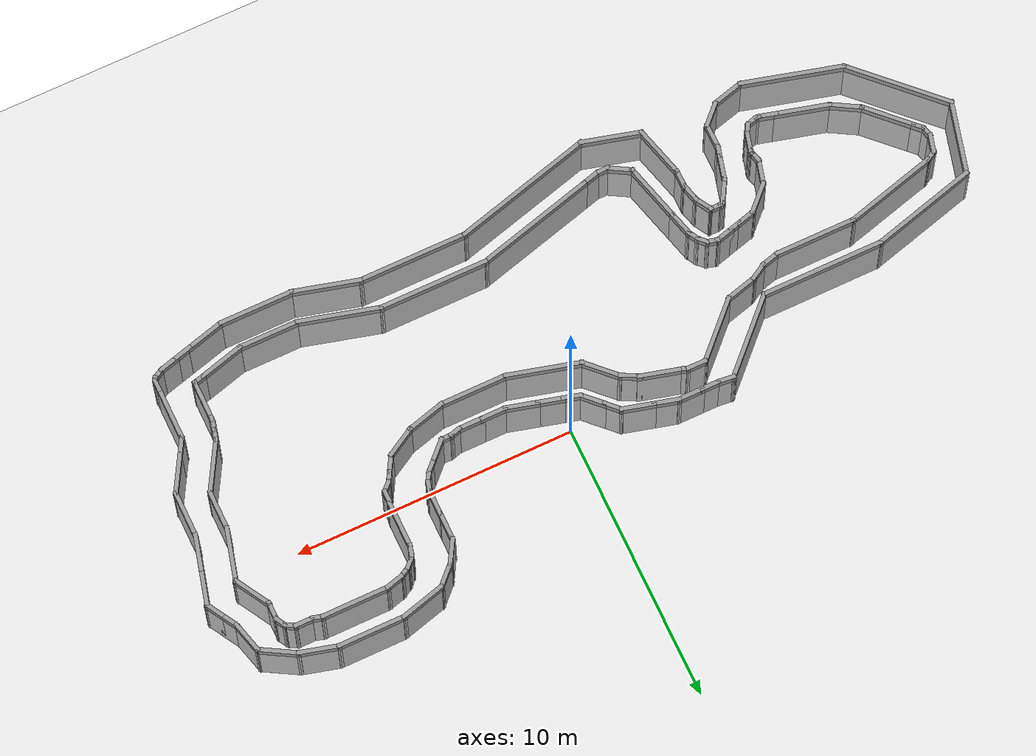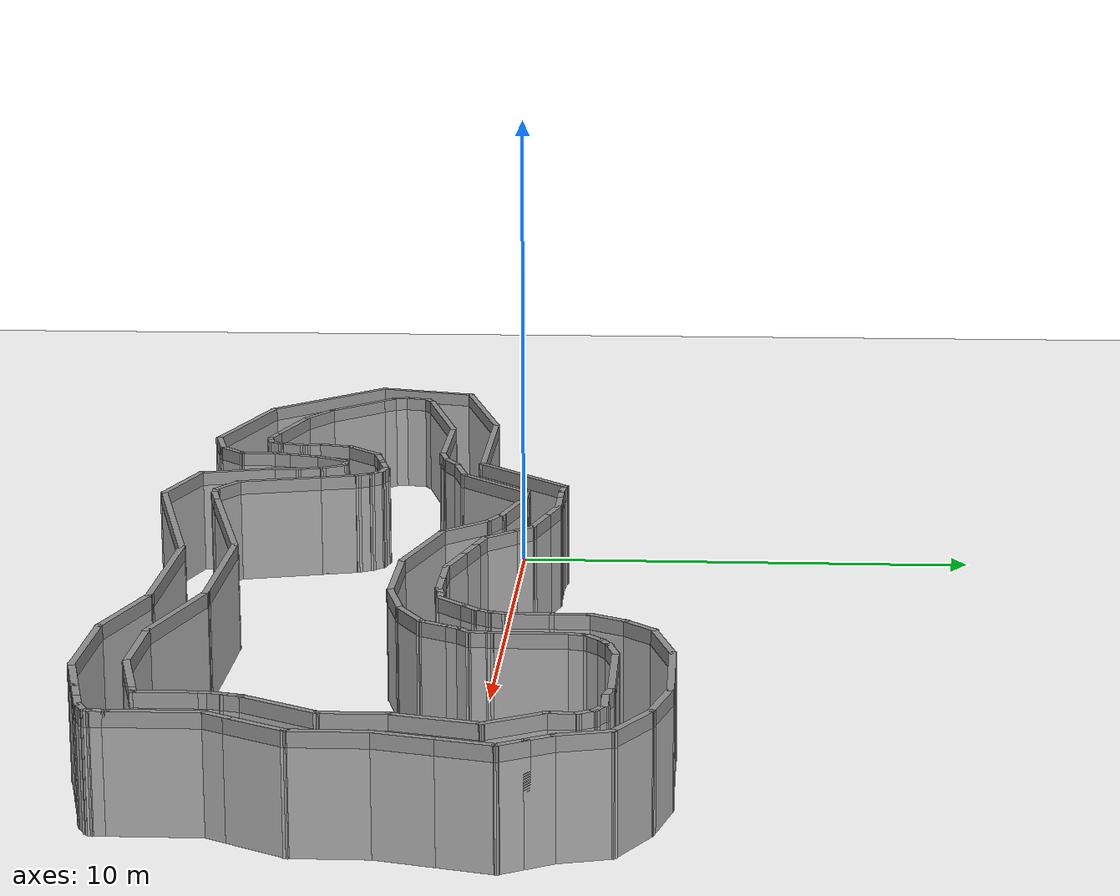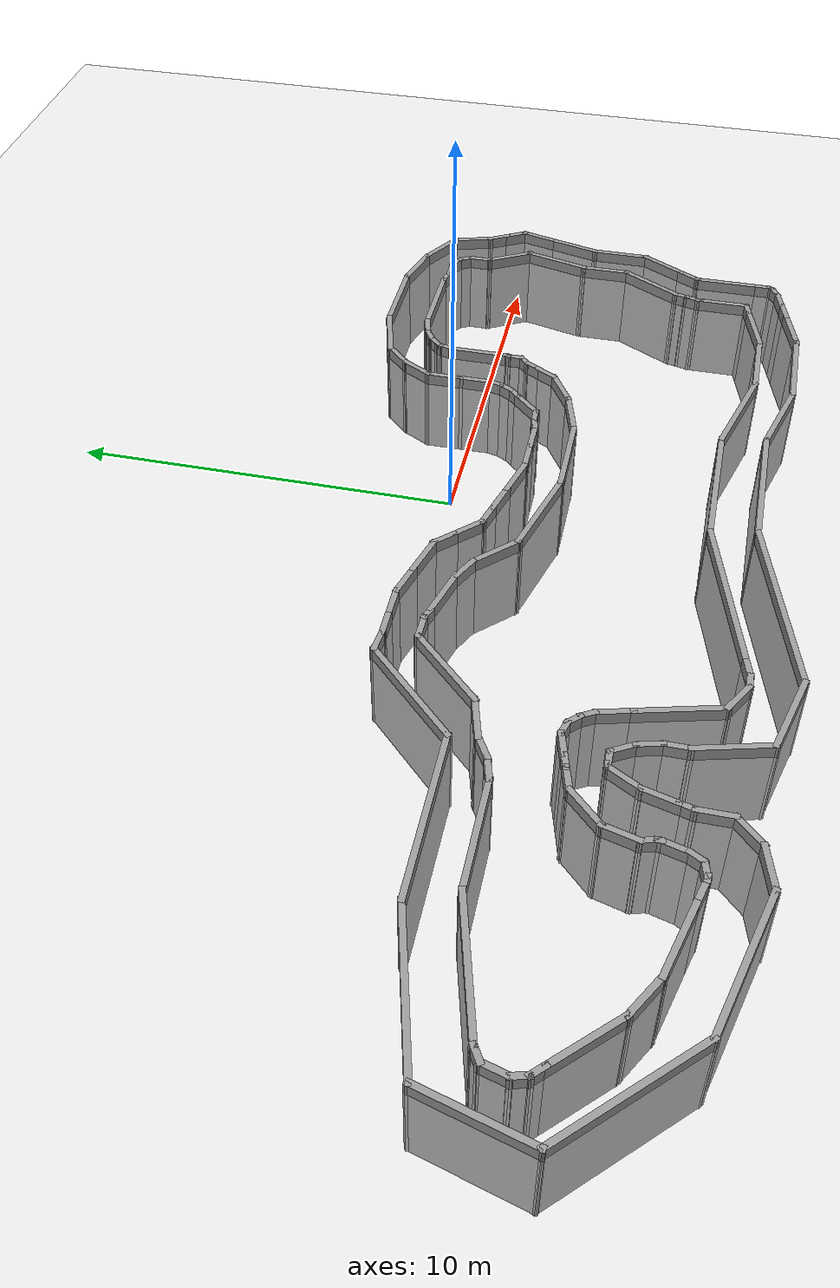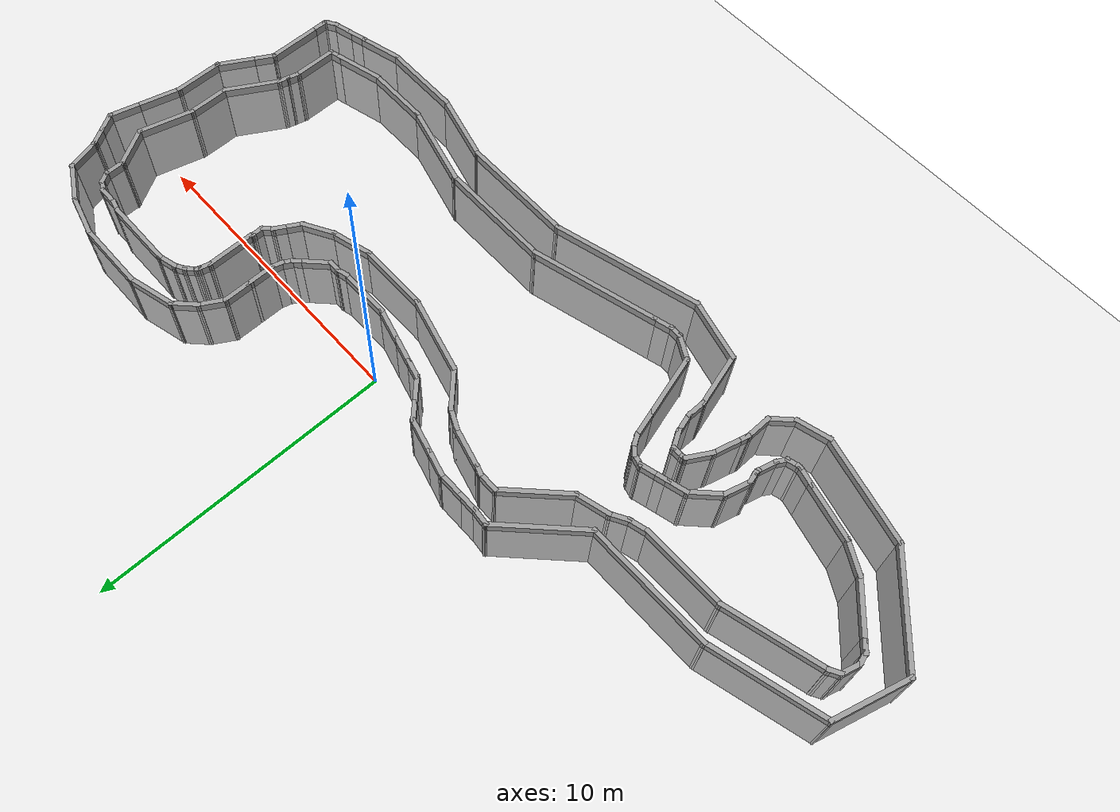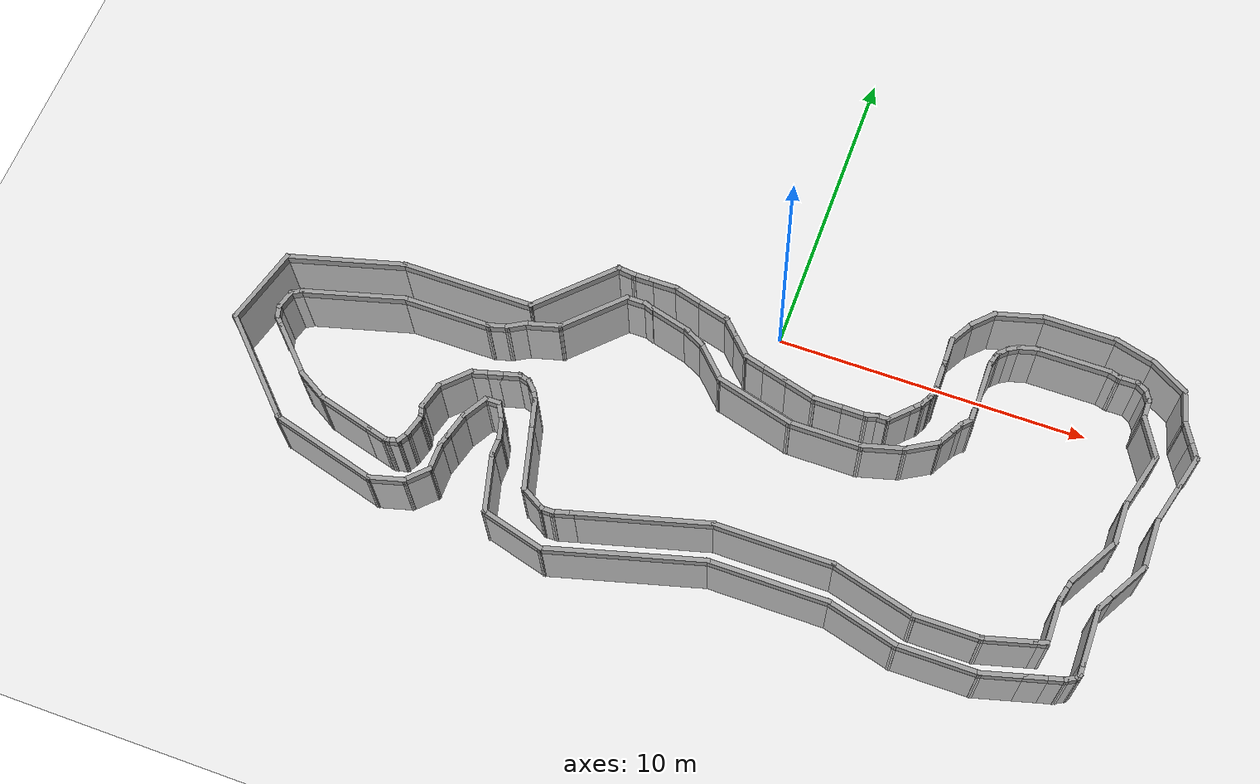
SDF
<sdf version="1.7">
 <world name="default">
  <light name="sun" type="directional">
   <pose>0 0 10 0 -0 0</pose>
   <diffuse>0.8 0.8 0.8 1</diffuse>
   <specular>0.2 0.2 0.2 1</specular>
   <attenuation>
    <range>1000</range>
    <constant>0.9</constant>
    <linear>0.01</linear>
    <quadratic>0.001</quadratic>
   </attenuation>
   <direction>-0.5 0.1 -0.9</direction>
   <spot><inner_angle>0</inner_angle><outer_angle>0</outer_angle><falloff>0</falloff></spot>
  </light>
  <model name="ground_plane">
   <static>1</static>
   <link name="link">
    <collision name="collision">
     <geometry><plane><normal>0 0 1</normal><size>100 100</size></plane></geometry>
     <surface>
      <contact><collide_bitmask>65535</collide_bitmask></contact>
      <friction><ode><mu>100</mu><mu2>50</mu2></ode></friction>
     </surface>
    </collision>
    <visual name="visual">
     <cast_shadows>0</cast_shadows>
     <geometry><plane><normal>0 0 1</normal><size>100 100</size></plane></geometry>
     <material>
      <script><uri>file://media/materials/scripts/gazebo.material</uri><name>Gazebo/Grey</name></script>
     </material>
    </visual>
   </link>
  </model>
  <gravity>0 0 -9.8</gravity>
  <magnetic_field>6e-06 2.3e-05 -4.2e-05</magnetic_field>
  <atmosphere type="adiabatic"/>
  <physics type="ode">
   <max_step_size>0.001</max_step_size>
   <real_time_factor>1</real_time_factor>
   <real_time_update_rate>1000</real_time_update_rate>
  </physics>
  <scene><ambient>0.4 0.4 0.4 1</ambient><background>0.7 0.7 0.7 1</background><shadows>1</shadows></scene>
  <spherical_coordinates>
   <surface_model>EARTH_WGS84</surface_model>
   <latitude_deg>0</latitude_deg>
   <longitude_deg>0</longitude_deg>
   <elevation>0</elevation>
   <heading_deg>0</heading_deg>
  </spherical_coordinates>
  <model name="race_track">
   <pose>-1.60501 -2.80737 -2.21385 0 -0 0</pose>
   <link name="Wall_0">
    <collision name="Wall_0_Collision">
     <geometry><box><size>3.25 0.15 2.5</size></box></geometry>
     <pose>0 0 1.25 0 -0 0</pose>
    </collision>
    <visual name="Wall_0_Visual">
     <pose>0 0 1.25 0 -0 0</pose>
     <geometry><box><size>3.25 0.15 2.5</size></box></geometry>
     <material>
      <script><uri>file://media/materials/scripts/gazebo.material</uri><name>Gazebo/Grey</name></script>
      <ambient>1 1 1 1</ambient>
     </material>
     <meta><layer>0</layer></meta>
    </visual>
    <pose>-5.20016 2.3234 0 0 -0 -2.35619</pose>
   </link>
   <link name="Wall_1">
    <collision name="Wall_1_Collision">
     <geometry><box><size>4.5 0.15 2.5</size></box></geometry>
     <pose>0 0 1.25 0 -0 0</pose>
    </collision>
    <visual name="Wall_1_Visual">
     <pose>0 0 1.25 0 -0 0</pose>
     <geometry><box><size>4.5 0.15 2.5</size></box></geometry>
     <material>
      <script><uri>file://media/materials/scripts/gazebo.material</uri><name>Gazebo/Grey</name></script>
      <ambient>1 1 1 1</ambient>
     </material>
     <meta><layer>0</layer></meta>
    </visual>
    <pose>-8.47118 1.22738 0 0 -0 3.14159</pose>
   </link>
   <link name="Wall_10">
    <collision name="Wall_10_Collision">
     <geometry><box><size>1 0.15 2.5</size></box></geometry>
     <pose>0 0 1.25 0 -0 0</pose>
    </collision>
    <visual name="Wall_10_Visual">
     <pose>0 0 1.25 0 -0 0</pose>
     <geometry><box><size>1 0.15 2.5</size></box></geometry>
     <material>
      <script><uri>file://media/materials/scripts/gazebo.material</uri><name>Gazebo/Grey</name></script>
      <ambient>1 1 1 1</ambient>
     </material>
     <meta><layer>0</layer></meta>
    </visual>
    <pose>-6.97408 -3.45025 0 0 -0 1.309</pose>
   </link>
   <link name="Wall_100">
    <collision name="Wall_100_Collision">
     <geometry><box><size>0.75 0.15 2.5</size></box></geometry>
     <pose>0 0 1.25 0 -0 0</pose>
    </collision>
    <visual name="Wall_100_Visual">
     <pose>0 0 1.25 0 -0 0</pose>
     <geometry><box><size>0.75 0.15 2.5</size></box></geometry>
     <material>
      <script><uri>file://media/materials/scripts/gazebo.material</uri><name>Gazebo/Grey</name></script>
      <ambient>1 1 1 1</ambient>
     </material>
     <meta><layer>0</layer></meta>
    </visual>
    <pose>-2.81623 -5.01276 0 0 -0 0.261799</pose>
   </link>
   <link name="Wall_101">
    <collision name="Wall_101_Collision">
     <geometry><box><size>4.5 0.15 2.5</size></box></geometry>
     <pose>0 0 1.25 0 -0 0</pose>
    </collision>
    <visual name="Wall_101_Visual">
     <pose>0 0 1.25 0 -0 0</pose>
     <geometry><box><size>4.5 0.15 2.5</size></box></geometry>
     <material>
      <script><uri>file://media/materials/scripts/gazebo.material</uri><name>Gazebo/Grey</name></script>
      <ambient>1 1 1 1</ambient>
     </material>
     <meta><layer>0</layer></meta>
    </visual>
    <pose>-0.425561 -4.37218 0 0 -0 0.261799</pose>
   </link>
   <link name="Wall_102">
    <collision name="Wall_102_Collision">
     <geometry><box><size>4 0.15 2.5</size></box></geometry>
     <pose>0 0 1.25 0 -0 0</pose>
    </collision>
    <visual name="Wall_102_Visual">
     <pose>0 0 1.25 0 -0 0</pose>
     <geometry><box><size>4 0.15 2.5</size></box></geometry>
     <material>
      <script><uri>file://media/materials/scripts/gazebo.material</uri><name>Gazebo/Grey</name></script>
      <ambient>1 1 1 1</ambient>
     </material>
     <meta><layer>0</layer></meta>
    </visual>
    <pose>3.60033 -3.80925 0 0 -0 0</pose>
   </link>
   <link name="Wall_103">
    <collision name="Wall_103_Collision">
     <geometry><box><size>3 0.15 2.5</size></box></geometry>
     <pose>0 0 1.25 0 -0 0</pose>
    </collision>
    <visual name="Wall_103_Visual">
     <pose>0 0 1.25 0 -0 0</pose>
     <geometry><box><size>3 0.15 2.5</size></box></geometry>
     <material>
      <script><uri>file://media/materials/scripts/gazebo.material</uri><name>Gazebo/Grey</name></script>
      <ambient>1 1 1 1</ambient>
     </material>
     <meta><layer>0</layer></meta>
    </visual>
    <pose>6.90177 -4.17807 0 0 -0 -0.261799</pose>
   </link>
   <link name="Wall_104">
    <collision name="Wall_104_Collision">
     <geometry><box><size>2.25 0.15 2.5</size></box></geometry>
     <pose>0 0 1.25 0 -0 0</pose>
    </collision>
    <visual name="Wall_104_Visual">
     <pose>0 0 1.25 0 -0 0</pose>
     <geometry><box><size>2.25 0.15 2.5</size></box></geometry>
     <material>
      <script><uri>file://media/materials/scripts/gazebo.material</uri><name>Gazebo/Grey</name></script>
      <ambient>1 1 1 1</ambient>
     </material>
     <meta><layer>0</layer></meta>
    </visual>
    <pose>9.32822 -4.54689 0 0 -0 0</pose>
   </link>
   <link name="Wall_105">
    <collision name="Wall_105_Collision">
     <geometry><box><size>1.75 0.15 2.5</size></box></geometry>
     <pose>0 0 1.25 0 -0 0</pose>
    </collision>
    <visual name="Wall_105_Visual">
     <pose>0 0 1.25 0 -0 0</pose>
     <geometry><box><size>1.75 0.15 2.5</size></box></geometry>
     <material>
      <script><uri>file://media/materials/scripts/gazebo.material</uri><name>Gazebo/Grey</name></script>
      <ambient>1 1 1 1</ambient>
     </material>
     <meta><layer>0</layer></meta>
    </visual>
    <pose>11.151 -4.33983 0 0 -0 0.261799</pose>
   </link>
   <link name="Wall_106">
    <collision name="Wall_106_Collision">
     <geometry><box><size>0.5 0.15 2.5</size></box></geometry>
     <pose>0 0 1.25 0 -0 0</pose>
    </collision>
    <visual name="Wall_106_Visual">
     <pose>0 0 1.25 0 -0 0</pose>
     <geometry><box><size>0.5 0.15 2.5</size></box></geometry>
     <material>
      <script><uri>file://media/materials/scripts/gazebo.material</uri><name>Gazebo/Grey</name></script>
      <ambient>1 1 1 1</ambient>
     </material>
     <meta><layer>0</layer></meta>
    </visual>
    <pose>12.0927 -4.08748 0 0 -0 0.261799</pose>
   </link>
   <link name="Wall_107">
    <collision name="Wall_107_Collision">
     <geometry><box><size>1.5 0.15 2.5</size></box></geometry>
     <pose>0 0 1.25 0 -0 0</pose>
    </collision>
    <visual name="Wall_107_Visual">
     <pose>0 0 1.25 0 -0 0</pose>
     <geometry><box><size>1.5 0.15 2.5</size></box></geometry>
     <material>
      <script><uri>file://media/materials/scripts/gazebo.material</uri><name>Gazebo/Grey</name></script>
      <ambient>1 1 1 1</ambient>
     </material>
     <meta><layer>0</layer></meta>
    </visual>
    <pose>12.2618 -3.36719 0 0 -0 1.5708</pose>
   </link>
   <link name="Wall_108">
    <collision name="Wall_108_Collision">
     <geometry><box><size>0.25 0.15 2.5</size></box></geometry>
     <pose>0 0 1.25 0 -0 0</pose>
    </collision>
    <visual name="Wall_108_Visual">
     <pose>0 0 1.25 0 -0 0</pose>
     <geometry><box><size>0.25 0.15 2.5</size></box></geometry>
     <material>
      <script><uri>file://media/materials/scripts/gazebo.material</uri><name>Gazebo/Grey</name></script>
      <ambient>1 1 1 1</ambient>
     </material>
     <meta><layer>0</layer></meta>
    </visual>
    <pose>12.2618 -2.64219 0 0 -0 1.5708</pose>
   </link>
   <link name="Wall_109">
    <collision name="Wall_109_Collision">
     <geometry><box><size>0.5 0.15 2.5</size></box></geometry>
     <pose>0 0 1.25 0 -0 0</pose>
    </collision>
    <visual name="Wall_109_Visual">
     <pose>0 0 1.25 0 -0 0</pose>
     <geometry><box><size>0.5 0.15 2.5</size></box></geometry>
     <material>
      <script><uri>file://media/materials/scripts/gazebo.material</uri><name>Gazebo/Grey</name></script>
      <ambient>1 1 1 1</ambient>
     </material>
     <meta><layer>0</layer></meta>
    </visual>
    <pose>12.3071 -2.42315 0 0 -0 1.309</pose>
   </link>
   <link name="Wall_11">
    <collision name="Wall_11_Collision">
     <geometry><box><size>1 0.15 2.5</size></box></geometry>
     <pose>0 0 1.25 0 -0 0</pose>
    </collision>
    <visual name="Wall_11_Visual">
     <pose>0 0 1.25 0 -0 0</pose>
     <geometry><box><size>1 0.15 2.5</size></box></geometry>
     <material>
      <script><uri>file://media/materials/scripts/gazebo.material</uri><name>Gazebo/Grey</name></script>
      <ambient>1 1 1 1</ambient>
     </material>
     <meta><layer>0</layer></meta>
    </visual>
    <pose>-6.65158 -2.67167 0 0 -0 1.0472</pose>
   </link>
   <link name="Wall_110">
    <collision name="Wall_110_Collision">
     <geometry><box><size>0.15 0.15 2.5</size></box></geometry>
     <pose>0 0 1.25 0 -0 0</pose>
    </collision>
    <visual name="Wall_110_Visual">
     <pose>0 0 1.25 0 -0 0</pose>
     <geometry><box><size>0.15 0.15 2.5</size></box></geometry>
     <material>
      <script><uri>file://media/materials/scripts/gazebo.material</uri><name>Gazebo/Grey</name></script>
      <ambient>1 1 1 1</ambient>
     </material>
     <meta><layer>0</layer></meta>
    </visual>
    <pose>12.3524 -2.25411 0 0 -0 0</pose>
   </link>
   <link name="Wall_111">
    <collision name="Wall_111_Collision">
     <geometry><box><size>0.5 0.15 2.5</size></box></geometry>
     <pose>0 0 1.25 0 -0 0</pose>
    </collision>
    <visual name="Wall_111_Visual">
     <pose>0 0 1.25 0 -0 0</pose>
     <geometry><box><size>0.5 0.15 2.5</size></box></geometry>
     <material>
      <script><uri>file://media/materials/scripts/gazebo.material</uri><name>Gazebo/Grey</name></script>
      <ambient>1 1 1 1</ambient>
     </material>
     <meta><layer>0</layer></meta>
    </visual>
    <pose>12.3977 -2.08508 0 0 -0 1.309</pose>
   </link>
   <link name="Wall_112">
    <collision name="Wall_112_Collision">
     <geometry><box><size>2 0.15 2.5</size></box></geometry>
     <pose>0 0 1.25 0 -0 0</pose>
    </collision>
    <visual name="Wall_112_Visual">
     <pose>0 0 1.25 0 -0 0</pose>
     <geometry><box><size>2 0.15 2.5</size></box></geometry>
     <material>
      <script><uri>file://media/materials/scripts/gazebo.material</uri><name>Gazebo/Grey</name></script>
      <ambient>1 1 1 1</ambient>
     </material>
     <meta><layer>0</layer></meta>
    </visual>
    <pose>12.9054 -1.11497 0 0 -0 1.0472</pose>
   </link>
   <link name="Wall_113">
    <collision name="Wall_113_Collision">
     <geometry><box><size>1.5 0.15 2.5</size></box></geometry>
     <pose>0 0 1.25 0 -0 0</pose>
    </collision>
    <visual name="Wall_113_Visual">
     <pose>0 0 1.25 0 -0 0</pose>
     <geometry><box><size>1.5 0.15 2.5</size></box></geometry>
     <material>
      <script><uri>file://media/materials/scripts/gazebo.material</uri><name>Gazebo/Grey</name></script>
      <ambient>1 1 1 1</ambient>
     </material>
     <meta><layer>0</layer></meta>
    </visual>
    <pose>13.3679 0.361107 0 0 -0 1.5708</pose>
   </link>
   <link name="Wall_114">
    <collision name="Wall_114_Collision">
     <geometry><box><size>2 0.15 2.5</size></box></geometry>
     <pose>0 0 1.25 0 -0 0</pose>
    </collision>
    <visual name="Wall_114_Visual">
     <pose>0 0 1.25 0 -0 0</pose>
     <geometry><box><size>2 0.15 2.5</size></box></geometry>
     <material>
      <script><uri>file://media/materials/scripts/gazebo.material</uri><name>Gazebo/Grey</name></script>
      <ambient>1 1 1 1</ambient>
     </material>
     <meta><layer>0</layer></meta>
    </visual>
    <pose>13.6074 1.92959 0 0 -0 1.309</pose>
   </link>
   <link name="Wall_115">
    <collision name="Wall_115_Collision">
     <geometry><box><size>1.5 0.15 2.5</size></box></geometry>
     <pose>0 0 1.25 0 -0 0</pose>
    </collision>
    <visual name="Wall_115_Visual">
     <pose>0 0 1.25 0 -0 0</pose>
     <geometry><box><size>1.5 0.15 2.5</size></box></geometry>
     <material>
      <script><uri>file://media/materials/scripts/gazebo.material</uri><name>Gazebo/Grey</name></script>
      <ambient>1 1 1 1</ambient>
     </material>
     <meta><layer>0</layer></meta>
    </visual>
    <pose>13.5093 3.40764 0 0 -0 2.0944</pose>
   </link>
   <link name="Wall_116">
    <collision name="Wall_116_Collision">
     <geometry><box><size>0.75 0.15 2.5</size></box></geometry>
     <pose>0 0 1.25 0 -0 0</pose>
    </collision>
    <visual name="Wall_116_Visual">
     <pose>0 0 1.25 0 -0 0</pose>
     <geometry><box><size>0.75 0.15 2.5</size></box></geometry>
     <material>
      <script><uri>file://media/materials/scripts/gazebo.material</uri><name>Gazebo/Grey</name></script>
      <ambient>1 1 1 1</ambient>
     </material>
     <meta><layer>0</layer></meta>
    </visual>
    <pose>13.1718 4.2922 0 0 -0 1.5708</pose>
   </link>
   <link name="Wall_117">
    <collision name="Wall_117_Collision">
     <geometry><box><size>0.5 0.15 2.5</size></box></geometry>
     <pose>0 0 1.25 0 -0 0</pose>
    </collision>
    <visual name="Wall_117_Visual">
     <pose>0 0 1.25 0 -0 0</pose>
     <geometry><box><size>0.5 0.15 2.5</size></box></geometry>
     <material>
      <script><uri>file://media/materials/scripts/gazebo.material</uri><name>Gazebo/Grey</name></script>
      <ambient>1 1 1 1</ambient>
     </material>
     <meta><layer>0</layer></meta>
    </visual>
    <pose>13.0843 4.74376 0 0 -0 2.0944</pose>
   </link>
   <link name="Wall_118">
    <collision name="Wall_118_Collision">
     <geometry><box><size>0.5 0.15 2.5</size></box></geometry>
     <pose>0 0 1.25 0 -0 0</pose>
    </collision>
    <visual name="Wall_118_Visual">
     <pose>0 0 1.25 0 -0 0</pose>
     <geometry><box><size>0.5 0.15 2.5</size></box></geometry>
     <material>
      <script><uri>file://media/materials/scripts/gazebo.material</uri><name>Gazebo/Grey</name></script>
      <ambient>1 1 1 1</ambient>
     </material>
     <meta><layer>0</layer></meta>
    </visual>
    <pose>12.8452 4.98281 0 0 -0 2.61799</pose>
   </link>
   <link name="Wall_119">
    <collision name="Wall_119_Collision">
     <geometry><box><size>0.75 0.15 2.5</size></box></geometry>
     <pose>0 0 1.25 0 -0 0</pose>
    </collision>
    <visual name="Wall_119_Visual">
     <pose>0 0 1.25 0 -0 0</pose>
     <geometry><box><size>0.75 0.15 2.5</size></box></geometry>
     <material>
      <script><uri>file://media/materials/scripts/gazebo.material</uri><name>Gazebo/Grey</name></script>
      <ambient>1 1 1 1</ambient>
     </material>
     <meta><layer>0</layer></meta>
    </visual>
    <pose>12.3937 5.07031 0 0 -0 3.14159</pose>
   </link>
   <link name="Wall_12">
    <collision name="Wall_12_Collision">
     <geometry><box><size>0.25 0.15 2.5</size></box></geometry>
     <pose>0 0 1.25 0 -0 0</pose>
    </collision>
    <visual name="Wall_12_Visual">
     <pose>0 0 1.25 0 -0 0</pose>
     <geometry><box><size>0.25 0.15 2.5</size></box></geometry>
     <material>
      <script><uri>file://media/materials/scripts/gazebo.material</uri><name>Gazebo/Grey</name></script>
      <ambient>1 1 1 1</ambient>
     </material>
     <meta><layer>0</layer></meta>
    </visual>
    <pose>-6.39079 -2.29067 0 0 -0 0.261799</pose>
   </link>
   <link name="Wall_120">
    <collision name="Wall_120_Collision">
     <geometry><box><size>0.5 0.15 2.5</size></box></geometry>
     <pose>0 0 1.25 0 -0 0</pose>
    </collision>
    <visual name="Wall_120_Visual">
     <pose>0 0 1.25 0 -0 0</pose>
     <geometry><box><size>0.5 0.15 2.5</size></box></geometry>
     <material>
      <script><uri>file://media/materials/scripts/gazebo.material</uri><name>Gazebo/Grey</name></script>
      <ambient>1 1 1 1</ambient>
     </material>
     <meta><layer>0</layer></meta>
    </visual>
    <pose>11.9246 5.11561 0 0 -0 2.87979</pose>
   </link>
   <link name="Wall_121">
    <collision name="Wall_121_Collision">
     <geometry><box><size>2.5 0.15 2.5</size></box></geometry>
     <pose>0 0 1.25 0 -0 0</pose>
    </collision>
    <visual name="Wall_121_Visual">
     <pose>0 0 1.25 0 -0 0</pose>
     <geometry><box><size>2.5 0.15 2.5</size></box></geometry>
     <material>
      <script><uri>file://media/materials/scripts/gazebo.material</uri><name>Gazebo/Grey</name></script>
      <ambient>1 1 1 1</ambient>
     </material>
     <meta><layer>0</layer></meta>
    </visual>
    <pose>10.5806 5.1609 0 0 -0 3.14159</pose>
   </link>
   <link name="Wall_122">
    <collision name="Wall_122_Collision">
     <geometry><box><size>0.75 0.15 2.5</size></box></geometry>
     <pose>0 0 1.25 0 -0 0</pose>
    </collision>
    <visual name="Wall_122_Visual">
     <pose>0 0 1.25 0 -0 0</pose>
     <geometry><box><size>0.75 0.15 2.5</size></box></geometry>
     <material>
      <script><uri>file://media/materials/scripts/gazebo.material</uri><name>Gazebo/Grey</name></script>
      <ambient>1 1 1 1</ambient>
     </material>
     <meta><layer>0</layer></meta>
    </visual>
    <pose>9.1158 5.08325 0 0 -0 -2.87979</pose>
   </link>
   <link name="Wall_123">
    <collision name="Wall_123_Collision">
     <geometry><box><size>0.5 0.15 2.5</size></box></geometry>
     <pose>0 0 1.25 0 -0 0</pose>
    </collision>
    <visual name="Wall_123_Visual">
     <pose>0 0 1.25 0 -0 0</pose>
     <geometry><box><size>0.5 0.15 2.5</size></box></geometry>
     <material>
      <script><uri>file://media/materials/scripts/gazebo.material</uri><name>Gazebo/Grey</name></script>
      <ambient>1 1 1 1</ambient>
     </material>
     <meta><layer>0</layer></meta>
    </visual>
    <pose>8.67447 4.91811 0 0 -0 -2.61799</pose>
   </link>
   <link name="Wall_124">
    <collision name="Wall_124_Collision">
     <geometry><box><size>0.5 0.15 2.5</size></box></geometry>
     <pose>0 0 1.25 0 -0 0</pose>
    </collision>
    <visual name="Wall_124_Visual">
     <pose>0 0 1.25 0 -0 0</pose>
     <geometry><box><size>0.5 0.15 2.5</size></box></geometry>
     <material>
      <script><uri>file://media/materials/scripts/gazebo.material</uri><name>Gazebo/Grey</name></script>
      <ambient>1 1 1 1</ambient>
     </material>
     <meta><layer>0</layer></meta>
    </visual>
    <pose>8.39917 4.70686 0 0 -0 -2.35619</pose>
   </link>
   <link name="Wall_125">
    <collision name="Wall_125_Collision">
     <geometry><box><size>0.25 0.15 2.5</size></box></geometry>
     <pose>0 0 1.25 0 -0 0</pose>
    </collision>
    <visual name="Wall_125_Visual">
     <pose>0 0 1.25 0 -0 0</pose>
     <geometry><box><size>0.25 0.15 2.5</size></box></geometry>
     <material>
      <script><uri>file://media/materials/scripts/gazebo.material</uri><name>Gazebo/Grey</name></script>
      <ambient>1 1 1 1</ambient>
     </material>
     <meta><layer>0</layer></meta>
    </visual>
    <pose>8.25043 4.53982 0 0 -0 -2.0944</pose>
   </link>
   <link name="Wall_126">
    <collision name="Wall_126_Collision">
     <geometry><box><size>0.5 0.15 2.5</size></box></geometry>
     <pose>0 0 1.25 0 -0 0</pose>
    </collision>
    <visual name="Wall_126_Visual">
     <pose>0 0 1.25 0 -0 0</pose>
     <geometry><box><size>0.5 0.15 2.5</size></box></geometry>
     <material>
      <script><uri>file://media/materials/scripts/gazebo.material</uri><name>Gazebo/Grey</name></script>
      <ambient>1 1 1 1</ambient>
     </material>
     <meta><layer>0</layer></meta>
    </visual>
    <pose>8.18013 4.32748 0 0 -0 -1.8326</pose>
   </link>
   <link name="Wall_127">
    <collision name="Wall_127_Collision">
     <geometry><box><size>1.75 0.15 2.5</size></box></geometry>
     <pose>0 0 1.25 0 -0 0</pose>
    </collision>
    <visual name="Wall_127_Visual">
     <pose>0 0 1.25 0 -0 0</pose>
     <geometry><box><size>1.75 0.15 2.5</size></box></geometry>
     <material>
      <script><uri>file://media/materials/scripts/gazebo.material</uri><name>Gazebo/Grey</name></script>
      <ambient>1 1 1 1</ambient>
     </material>
     <meta><layer>0</layer></meta>
    </visual>
    <pose>8.13484 3.35844 0 0 -0 -1.5708</pose>
   </link>
   <link name="Wall_128">
    <collision name="Wall_128_Collision">
     <geometry><box><size>0.25 0.15 2.5</size></box></geometry>
     <pose>0 0 1.25 0 -0 0</pose>
    </collision>
    <visual name="Wall_128_Visual">
     <pose>0 0 1.25 0 -0 0</pose>
     <geometry><box><size>0.25 0.15 2.5</size></box></geometry>
     <material>
      <script><uri>file://media/materials/scripts/gazebo.material</uri><name>Gazebo/Grey</name></script>
      <ambient>1 1 1 1</ambient>
     </material>
     <meta><layer>0</layer></meta>
    </visual>
    <pose>8.1219 2.51015 0 0 -0 -1.8326</pose>
   </link>
   <link name="Wall_129">
    <collision name="Wall_129_Collision">
     <geometry><box><size>0.5 0.15 2.5</size></box></geometry>
     <pose>0 0 1.25 0 -0 0</pose>
    </collision>
    <visual name="Wall_129_Visual">
     <pose>0 0 1.25 0 -0 0</pose>
     <geometry><box><size>0.5 0.15 2.5</size></box></geometry>
     <material>
      <script><uri>file://media/materials/scripts/gazebo.material</uri><name>Gazebo/Grey</name></script>
      <ambient>1 1 1 1</ambient>
     </material>
     <meta><layer>0</layer></meta>
    </visual>
    <pose>8.10896 2.28685 0 0 -0 -1.5708</pose>
   </link>
   <link name="Wall_13">
    <collision name="Wall_13_Collision">
     <geometry><box><size>0.5 0.15 2.5</size></box></geometry>
     <pose>0 0 1.25 0 -0 0</pose>
    </collision>
    <visual name="Wall_13_Visual">
     <pose>0 0 1.25 0 -0 0</pose>
     <geometry><box><size>0.5 0.15 2.5</size></box></geometry>
     <material>
      <script><uri>file://media/materials/scripts/gazebo.material</uri><name>Gazebo/Grey</name></script>
      <ambient>1 1 1 1</ambient>
     </material>
     <meta><layer>0</layer></meta>
    </visual>
    <pose>-6.16749 -2.27773 0 0 -0 0</pose>
   </link>
   <link name="Wall_130">
    <collision name="Wall_130_Collision">
     <geometry><box><size>0.5 0.15 2.5</size></box></geometry>
     <pose>0 0 1.25 0 -0 0</pose>
    </collision>
    <visual name="Wall_130_Visual">
     <pose>0 0 1.25 0 -0 0</pose>
     <geometry><box><size>0.5 0.15 2.5</size></box></geometry>
     <material>
      <script><uri>file://media/materials/scripts/gazebo.material</uri><name>Gazebo/Grey</name></script>
      <ambient>1 1 1 1</ambient>
     </material>
     <meta><layer>0</layer></meta>
    </visual>
    <pose>7.98521 1.98811 0 0 -0 -2.35619</pose>
   </link>
   <link name="Wall_131">
    <collision name="Wall_131_Collision">
     <geometry><box><size>0.5 0.15 2.5</size></box></geometry>
     <pose>0 0 1.25 0 -0 0</pose>
    </collision>
    <visual name="Wall_131_Visual">
     <pose>0 0 1.25 0 -0 0</pose>
     <geometry><box><size>0.5 0.15 2.5</size></box></geometry>
     <material>
      <script><uri>file://media/materials/scripts/gazebo.material</uri><name>Gazebo/Grey</name></script>
      <ambient>1 1 1 1</ambient>
     </material>
     <meta><layer>0</layer></meta>
    </visual>
    <pose>7.77397 1.71281 0 0 -0 -2.0944</pose>
   </link>
   <link name="Wall_132">
    <collision name="Wall_132_Collision">
     <geometry><box><size>0.75 0.15 2.5</size></box></geometry>
     <pose>0 0 1.25 0 -0 0</pose>
    </collision>
    <visual name="Wall_132_Visual">
     <pose>0 0 1.25 0 -0 0</pose>
     <geometry><box><size>0.75 0.15 2.5</size></box></geometry>
     <material>
      <script><uri>file://media/materials/scripts/gazebo.material</uri><name>Gazebo/Grey</name></script>
      <ambient>1 1 1 1</ambient>
     </material>
     <meta><layer>0</layer></meta>
    </visual>
    <pose>7.53647 1.30145 0 0 -0 -2.0944</pose>
   </link>
   <link name="Wall_133">
    <collision name="Wall_133_Collision">
     <geometry><box><size>1.25 0.15 2.5</size></box></geometry>
     <pose>0 0 1.25 0 -0 0</pose>
    </collision>
    <visual name="Wall_133_Visual">
     <pose>0 0 1.25 0 -0 0</pose>
     <geometry><box><size>1.25 0.15 2.5</size></box></geometry>
     <material>
      <script><uri>file://media/materials/scripts/gazebo.material</uri><name>Gazebo/Grey</name></script>
      <ambient>1 1 1 1</ambient>
     </material>
     <meta><layer>0</layer></meta>
    </visual>
    <pose>6.91016 0.76664 0 0 -0 -2.61799</pose>
   </link>
   <link name="Wall_134">
    <collision name="Wall_134_Collision">
     <geometry><box><size>1.5 0.15 2.5</size></box></geometry>
     <pose>0 0 1.25 0 -0 0</pose>
    </collision>
    <visual name="Wall_134_Visual">
     <pose>0 0 1.25 0 -0 0</pose>
     <geometry><box><size>1.5 0.15 2.5</size></box></geometry>
     <material>
      <script><uri>file://media/materials/scripts/gazebo.material</uri><name>Gazebo/Grey</name></script>
      <ambient>1 1 1 1</ambient>
     </material>
     <meta><layer>0</layer></meta>
    </visual>
    <pose>5.78184 0.316937 0 0 -0 -2.87979</pose>
   </link>
   <link name="Wall_135">
    <collision name="Wall_135_Collision">
     <geometry><box><size>2.5 0.15 2.5</size></box></geometry>
     <pose>0 0 1.25 0 -0 0</pose>
    </collision>
    <visual name="Wall_135_Visual">
     <pose>0 0 1.25 0 -0 0</pose>
     <geometry><box><size>2.5 0.15 2.5</size></box></geometry>
     <material>
      <script><uri>file://media/materials/scripts/gazebo.material</uri><name>Gazebo/Grey</name></script>
      <ambient>1 1 1 1</ambient>
     </material>
     <meta><layer>0</layer></meta>
    </visual>
    <pose>3.95484 0.142234 0 0 -0 3.14159</pose>
   </link>
   <link name="Wall_136">
    <collision name="Wall_136_Collision">
     <geometry><box><size>2.75 0.15 2.5</size></box></geometry>
     <pose>0 0 1.25 0 -0 0</pose>
    </collision>
    <visual name="Wall_136_Visual">
     <pose>0 0 1.25 0 -0 0</pose>
     <geometry><box><size>2.75 0.15 2.5</size></box></geometry>
     <material>
      <script><uri>file://media/materials/scripts/gazebo.material</uri><name>Gazebo/Grey</name></script>
      <ambient>1 1 1 1</ambient>
     </material>
     <meta><layer>0</layer></meta>
    </visual>
    <pose>1.52414 0.478699 0 0 -0 2.87979</pose>
   </link>
   <link name="Wall_137">
    <collision name="Wall_137_Collision">
     <geometry><box><size>1.5 0.15 2.5</size></box></geometry>
     <pose>0 0 1.25 0 -0 0</pose>
    </collision>
    <visual name="Wall_137_Visual">
     <pose>0 0 1.25 0 -0 0</pose>
     <geometry><box><size>1.5 0.15 2.5</size></box></geometry>
     <material>
      <script><uri>file://media/materials/scripts/gazebo.material</uri><name>Gazebo/Grey</name></script>
      <ambient>1 1 1 1</ambient>
     </material>
     <meta><layer>0</layer></meta>
    </visual>
    <pose>-0.208862 1.29246 0 0 -0 2.35619</pose>
   </link>
   <link name="Wall_138">
    <collision name="Wall_138_Collision">
     <geometry><box><size>0.83217 0.15 2.5</size></box></geometry>
     <pose>0 0 1.25 0 -0 0</pose>
    </collision>
    <visual name="Wall_138_Visual">
     <pose>0 0 1.25 0 -0 0</pose>
     <geometry><box><size>0.83217 0.15 2.5</size></box></geometry>
     <material>
      <script><uri>file://media/materials/scripts/gazebo.material</uri><name>Gazebo/Grey</name></script>
      <ambient>1 1 1 1</ambient>
     </material>
     <meta><layer>0</layer></meta>
    </visual>
    <pose>-0.992491 1.91976 0 0 -0 2.68625</pose>
   </link>
   <link name="Wall_139">
    <collision name="Wall_139_Collision">
     <geometry><box><size>1.5 0.15 2.5</size></box></geometry>
     <pose>0 0 1.25 0 -0 0</pose>
    </collision>
    <visual name="Wall_139_Visual">
     <pose>0 0 1.25 0 -0 0</pose>
     <geometry><box><size>1.5 0.15 2.5</size></box></geometry>
     <material>
      <script><uri>file://media/materials/scripts/gazebo.material</uri><name>Gazebo/Grey</name></script>
      <ambient>1 1 1 1</ambient>
     </material>
     <meta><layer>0</layer></meta>
    </visual>
    <pose>-1.9043 2.24446 0 0 -0 2.87979</pose>
   </link>
   <link name="Wall_14">
    <collision name="Wall_14_Collision">
     <geometry><box><size>0.75 0.15 2.5</size></box></geometry>
     <pose>0 0 1.25 0 -0 0</pose>
    </collision>
    <visual name="Wall_14_Visual">
     <pose>0 0 1.25 0 -0 0</pose>
     <geometry><box><size>0.75 0.15 2.5</size></box></geometry>
     <material>
      <script><uri>file://media/materials/scripts/gazebo.material</uri><name>Gazebo/Grey</name></script>
      <ambient>1 1 1 1</ambient>
     </material>
     <meta><layer>0</layer></meta>
    </visual>
    <pose>-5.84249 -2.53754 0 0 -0 -1.0472</pose>
   </link>
   <link name="Wall_140">
    <collision name="Wall_140_Collision">
     <geometry><box><size>0.411235 0.15 2.5</size></box></geometry>
     <pose>0 0 1.25 0 -0 0</pose>
    </collision>
    <visual name="Wall_140_Visual">
     <pose>0 0 1.25 0 -0 0</pose>
     <geometry><box><size>0.411235 0.15 2.5</size></box></geometry>
     <material>
      <script><uri>file://media/materials/scripts/gazebo.material</uri><name>Gazebo/Grey</name></script>
      <ambient>1 1 1 1</ambient>
     </material>
     <meta><layer>0</layer></meta>
    </visual>
    <pose>-2.72533 2.46446 0 0 -0 2.78748</pose>
   </link>
   <link name="Wall_141">
    <collision name="Wall_141_Collision">
     <geometry><box><size>0.788881 0.15 2.5</size></box></geometry>
     <pose>0 0 1.25 0 -0 0</pose>
    </collision>
    <visual name="Wall_141_Visual">
     <pose>0 0 1.25 0 -0 0</pose>
     <geometry><box><size>0.788881 0.15 2.5</size></box></geometry>
     <material>
      <script><uri>file://media/materials/scripts/gazebo.material</uri><name>Gazebo/Grey</name></script>
      <ambient>1 1 1 1</ambient>
     </material>
     <meta><layer>0</layer></meta>
    </visual>
    <pose>-3.16728 2.51238 0 0 -0 3.13335</pose>
   </link>
   <link name="Wall_15">
    <collision name="Wall_15_Collision">
     <geometry><box><size>0.75 0.15 2.5</size></box></geometry>
     <pose>0 0 1.25 0 -0 0</pose>
    </collision>
    <visual name="Wall_15_Visual">
     <pose>0 0 1.25 0 -0 0</pose>
     <geometry><box><size>0.75 0.15 2.5</size></box></geometry>
     <material>
      <script><uri>file://media/materials/scripts/gazebo.material</uri><name>Gazebo/Grey</name></script>
      <ambient>1 1 1 1</ambient>
     </material>
     <meta><layer>0</layer></meta>
    </visual>
    <pose>-5.61484 -3.08712 0 0 -0 -1.309</pose>
   </link>
   <link name="Wall_16">
    <collision name="Wall_16_Collision">
     <geometry><box><size>0.75 0.15 2.5</size></box></geometry>
     <pose>0 0 1.25 0 -0 0</pose>
    </collision>
    <visual name="Wall_16_Visual">
     <pose>0 0 1.25 0 -0 0</pose>
     <geometry><box><size>0.75 0.15 2.5</size></box></geometry>
     <material>
      <script><uri>file://media/materials/scripts/gazebo.material</uri><name>Gazebo/Grey</name></script>
      <ambient>1 1 1 1</ambient>
     </material>
     <meta><layer>0</layer></meta>
    </visual>
    <pose>-5.5372 -3.6769 0 0 -0 -1.5708</pose>
   </link>
   <link name="Wall_17">
    <collision name="Wall_17_Collision">
     <geometry><box><size>2 0.15 2.5</size></box></geometry>
     <pose>0 0 1.25 0 -0 0</pose>
    </collision>
    <visual name="Wall_17_Visual">
     <pose>0 0 1.25 0 -0 0</pose>
     <geometry><box><size>2 0.15 2.5</size></box></geometry>
     <material>
      <script><uri>file://media/materials/scripts/gazebo.material</uri><name>Gazebo/Grey</name></script>
      <ambient>1 1 1 1</ambient>
     </material>
     <meta><layer>0</layer></meta>
    </visual>
    <pose>-5.29779 -4.87038 0 0 -0 -1.309</pose>
   </link>
   <link name="Wall_18">
    <collision name="Wall_18_Collision">
     <geometry><box><size>2.25 0.15 2.5</size></box></geometry>
     <pose>0 0 1.25 0 -0 0</pose>
    </collision>
    <visual name="Wall_18_Visual">
     <pose>0 0 1.25 0 -0 0</pose>
     <geometry><box><size>2.25 0.15 2.5</size></box></geometry>
     <material>
      <script><uri>file://media/materials/scripts/gazebo.material</uri><name>Gazebo/Grey</name></script>
      <ambient>1 1 1 1</ambient>
     </material>
     <meta><layer>0</layer></meta>
    </visual>
    <pose>-4.04416 -6.03562 0 0 -0 -0.261799</pose>
   </link>
   <link name="Wall_19">
    <collision name="Wall_19_Collision">
     <geometry><box><size>5.25 0.15 2.5</size></box></geometry>
     <pose>0 0 1.25 0 -0 0</pose>
    </collision>
    <visual name="Wall_19_Visual">
     <pose>0 0 1.25 0 -0 0</pose>
     <geometry><box><size>5.25 0.15 2.5</size></box></geometry>
     <material>
      <script><uri>file://media/materials/scripts/gazebo.material</uri><name>Gazebo/Grey</name></script>
      <ambient>1 1 1 1</ambient>
     </material>
     <meta><layer>0</layer></meta>
    </visual>
    <pose>-0.566829 -5.64739 0 0 -0 0.261799</pose>
   </link>
   <link name="Wall_2">
    <collision name="Wall_2_Collision">
     <geometry><box><size>4 0.15 2.5</size></box></geometry>
     <pose>0 0 1.25 0 -0 0</pose>
    </collision>
    <visual name="Wall_2_Visual">
     <pose>0 0 1.25 0 -0 0</pose>
     <geometry><box><size>4 0.15 2.5</size></box></geometry>
     <material>
      <script><uri>file://media/materials/scripts/gazebo.material</uri><name>Gazebo/Grey</name></script>
      <ambient>1 1 1 1</ambient>
     </material>
     <meta><layer>0</layer></meta>
    </visual>
    <pose>-12.5056 0.729158 0 0 -0 -2.87979</pose>
   </link>
   <link name="Wall_20">
    <collision name="Wall_20_Collision">
     <geometry><box><size>4 0.15 2.5</size></box></geometry>
     <pose>0 0 1.25 0 -0 0</pose>
    </collision>
    <visual name="Wall_20_Visual">
     <pose>0 0 1.25 0 -0 0</pose>
     <geometry><box><size>4 0.15 2.5</size></box></geometry>
     <material>
      <script><uri>file://media/materials/scripts/gazebo.material</uri><name>Gazebo/Grey</name></script>
      <ambient>1 1 1 1</ambient>
     </material>
     <meta><layer>0</layer></meta>
    </visual>
    <pose>3.82128 -4.98741 0 0 -0 0</pose>
   </link>
   <link name="Wall_21">
    <collision name="Wall_21_Collision">
     <geometry><box><size>2.5 0.15 2.5</size></box></geometry>
     <pose>0 0 1.25 0 -0 0</pose>
    </collision>
    <visual name="Wall_21_Visual">
     <pose>0 0 1.25 0 -0 0</pose>
     <geometry><box><size>2.5 0.15 2.5</size></box></geometry>
     <material>
      <script><uri>file://media/materials/scripts/gazebo.material</uri><name>Gazebo/Grey</name></script>
      <ambient>1 1 1 1</ambient>
     </material>
     <meta><layer>0</layer></meta>
    </visual>
    <pose>6.88124 -5.29152 0 0 -0 -0.261799</pose>
   </link>
   <link name="Wall_22">
    <collision name="Wall_22_Collision">
     <geometry><box><size>2.75 0.15 2.5</size></box></geometry>
     <pose>0 0 1.25 0 -0 0</pose>
    </collision>
    <visual name="Wall_22_Visual">
     <pose>0 0 1.25 0 -0 0</pose>
     <geometry><box><size>2.75 0.15 2.5</size></box></geometry>
     <material>
      <script><uri>file://media/materials/scripts/gazebo.material</uri><name>Gazebo/Grey</name></script>
      <ambient>1 1 1 1</ambient>
     </material>
     <meta><layer>0</layer></meta>
    </visual>
    <pose>9.31621 -5.59563 0 0 -0 0</pose>
   </link>
   <link name="Wall_23">
    <collision name="Wall_23_Collision">
     <geometry><box><size>1.5 0.15 2.5</size></box></geometry>
     <pose>0 0 1.25 0 -0 0</pose>
    </collision>
    <visual name="Wall_23_Visual">
     <pose>0 0 1.25 0 -0 0</pose>
     <geometry><box><size>1.5 0.15 2.5</size></box></geometry>
     <material>
      <script><uri>file://media/materials/scripts/gazebo.material</uri><name>Gazebo/Grey</name></script>
      <ambient>1 1 1 1</ambient>
     </material>
     <meta><layer>0</layer></meta>
    </visual>
    <pose>11.2682 -5.42093 0 0 -0 0.261799</pose>
   </link>
   <link name="Wall_24">
    <collision name="Wall_24_Collision">
     <geometry><box><size>0.75 0.15 2.5</size></box></geometry>
     <pose>0 0 1.25 0 -0 0</pose>
    </collision>
    <visual name="Wall_24_Visual">
     <pose>0 0 1.25 0 -0 0</pose>
     <geometry><box><size>0.75 0.15 2.5</size></box></geometry>
     <material>
      <script><uri>file://media/materials/scripts/gazebo.material</uri><name>Gazebo/Grey</name></script>
      <ambient>1 1 1 1</ambient>
     </material>
     <meta><layer>0</layer></meta>
    </visual>
    <pose>12.21 -5.16858 0 0 -0 0.261799</pose>
   </link>
   <link name="Wall_25">
    <collision name="Wall_25_Collision">
     <geometry><box><size>0.75 0.15 2.5</size></box></geometry>
     <pose>0 0 1.25 0 -0 0</pose>
    </collision>
    <visual name="Wall_25_Visual">
     <pose>0 0 1.25 0 -0 0</pose>
     <geometry><box><size>0.75 0.15 2.5</size></box></geometry>
     <material>
      <script><uri>file://media/materials/scripts/gazebo.material</uri><name>Gazebo/Grey</name></script>
      <ambient>1 1 1 1</ambient>
     </material>
     <meta><layer>0</layer></meta>
    </visual>
    <pose>12.7895 -5.01329 0 0 -0 0.261799</pose>
   </link>
   <link name="Wall_26">
    <collision name="Wall_26_Collision">
     <geometry><box><size>0.5 0.15 2.5</size></box></geometry>
     <pose>0 0 1.25 0 -0 0</pose>
    </collision>
    <visual name="Wall_26_Visual">
     <pose>0 0 1.25 0 -0 0</pose>
     <geometry><box><size>0.5 0.15 2.5</size></box></geometry>
     <material>
      <script><uri>file://media/materials/scripts/gazebo.material</uri><name>Gazebo/Grey</name></script>
      <ambient>1 1 1 1</ambient>
     </material>
     <meta><layer>0</layer></meta>
    </visual>
    <pose>13.2309 -4.84814 0 0 -0 0.523599</pose>
   </link>
   <link name="Wall_27">
    <collision name="Wall_27_Collision">
     <geometry><box><size>0.25 0.15 2.5</size></box></geometry>
     <pose>0 0 1.25 0 -0 0</pose>
    </collision>
    <visual name="Wall_27_Visual">
     <pose>0 0 1.25 0 -0 0</pose>
     <geometry><box><size>0.25 0.15 2.5</size></box></geometry>
     <material>
      <script><uri>file://media/materials/scripts/gazebo.material</uri><name>Gazebo/Grey</name></script>
      <ambient>1 1 1 1</ambient>
     </material>
     <meta><layer>0</layer></meta>
    </visual>
    <pose>13.4074 -4.71734 0 0 -0 1.0472</pose>
   </link>
   <link name="Wall_28">
    <collision name="Wall_28_Collision">
     <geometry><box><size>0.5 0.15 2.5</size></box></geometry>
     <pose>0 0 1.25 0 -0 0</pose>
    </collision>
    <visual name="Wall_28_Visual">
     <pose>0 0 1.25 0 -0 0</pose>
     <geometry><box><size>0.5 0.15 2.5</size></box></geometry>
     <material>
      <script><uri>file://media/materials/scripts/gazebo.material</uri><name>Gazebo/Grey</name></script>
      <ambient>1 1 1 1</ambient>
     </material>
     <meta><layer>0</layer></meta>
    </visual>
    <pose>13.4324 -4.49904 0 0 -0 1.5708</pose>
   </link>
   <link name="Wall_3">
    <collision name="Wall_3_Collision">
     <geometry><box><size>2.75 0.15 2.5</size></box></geometry>
     <pose>0 0 1.25 0 -0 0</pose>
    </collision>
    <visual name="Wall_3_Visual">
     <pose>0 0 1.25 0 -0 0</pose>
     <geometry><box><size>2.75 0.15 2.5</size></box></geometry>
     <material>
      <script><uri>file://media/materials/scripts/gazebo.material</uri><name>Gazebo/Grey</name></script>
      <ambient>1 1 1 1</ambient>
     </material>
     <meta><layer>0</layer></meta>
    </visual>
    <pose>-14.7015 -1.02477 0 0 -0 -1.8326</pose>
   </link>
   <link name="Wall_30">
    <collision name="Wall_30_Collision">
     <geometry><box><size>2 0.15 2.5</size></box></geometry>
     <pose>0 0 1.25 0 -0 0</pose>
    </collision>
    <visual name="Wall_30_Visual">
     <pose>0 0 1.25 0 -0 0</pose>
     <geometry><box><size>2 0.15 2.5</size></box></geometry>
     <material>
      <script><uri>file://media/materials/scripts/gazebo.material</uri><name>Gazebo/Grey</name></script>
      <ambient>1 1 1 1</ambient>
     </material>
     <meta><layer>0</layer></meta>
    </visual>
    <pose>13.4324 -3.39904 0 0 -0 1.5708</pose>
   </link>
   <link name="Wall_31">
    <collision name="Wall_31_Collision">
     <geometry><box><size>0.75 0.15 2.5</size></box></geometry>
     <pose>0 0 1.25 0 -0 0</pose>
    </collision>
    <visual name="Wall_31_Visual">
     <pose>0 0 1.25 0 -0 0</pose>
     <geometry><box><size>0.75 0.15 2.5</size></box></geometry>
     <material>
      <script><uri>file://media/materials/scripts/gazebo.material</uri><name>Gazebo/Grey</name></script>
      <ambient>1 1 1 1</ambient>
     </material>
     <meta><layer>0</layer></meta>
    </visual>
    <pose>13.5824 -2.21423 0 0 -0 1.0472</pose>
   </link>
   <link name="Wall_32">
    <collision name="Wall_32_Collision">
     <geometry><box><size>1.5 0.15 2.5</size></box></geometry>
     <pose>0 0 1.25 0 -0 0</pose>
    </collision>
    <visual name="Wall_32_Visual">
     <pose>0 0 1.25 0 -0 0</pose>
     <geometry><box><size>1.5 0.15 2.5</size></box></geometry>
     <material>
      <script><uri>file://media/materials/scripts/gazebo.material</uri><name>Gazebo/Grey</name></script>
      <ambient>1 1 1 1</ambient>
     </material>
     <meta><layer>0</layer></meta>
    </visual>
    <pose>14.0699 -1.36986 0 0 -0 1.0472</pose>
   </link>
   <link name="Wall_33">
    <collision name="Wall_33_Collision">
     <geometry><box><size>1.75 0.15 2.5</size></box></geometry>
     <pose>0 0 1.25 0 -0 0</pose>
    </collision>
    <visual name="Wall_33_Visual">
     <pose>0 0 1.25 0 -0 0</pose>
     <geometry><box><size>1.75 0.15 2.5</size></box></geometry>
     <material>
      <script><uri>file://media/materials/scripts/gazebo.material</uri><name>Gazebo/Grey</name></script>
      <ambient>1 1 1 1</ambient>
     </material>
     <meta><layer>0</layer></meta>
    </visual>
    <pose>14.4074 0.01471 0 0 -0 1.5708</pose>
   </link>
   <link name="Wall_34">
    <collision name="Wall_34_Collision">
     <geometry><box><size>1.5 0.15 2.5</size></box></geometry>
     <pose>0 0 1.25 0 -0 0</pose>
    </collision>
    <visual name="Wall_34_Visual">
     <pose>0 0 1.25 0 -0 0</pose>
     <geometry><box><size>1.5 0.15 2.5</size></box></geometry>
     <material>
      <script><uri>file://media/materials/scripts/gazebo.material</uri><name>Gazebo/Grey</name></script>
      <ambient>1 1 1 1</ambient>
     </material>
     <meta><layer>0</layer></meta>
    </visual>
    <pose>14.5821 1.46671 0 0 -0 1.309</pose>
   </link>
   <link name="Wall_35">
    <collision name="Wall_35_Collision">
     <geometry><box><size>1.25 0.15 2.5</size></box></geometry>
     <pose>0 0 1.25 0 -0 0</pose>
    </collision>
    <visual name="Wall_35_Visual">
     <pose>0 0 1.25 0 -0 0</pose>
     <geometry><box><size>1.25 0.15 2.5</size></box></geometry>
     <material>
      <script><uri>file://media/materials/scripts/gazebo.material</uri><name>Gazebo/Grey</name></script>
      <ambient>1 1 1 1</ambient>
     </material>
     <meta><layer>0</layer></meta>
    </visual>
    <pose>14.8992 2.64997 0 0 -0 1.309</pose>
   </link>
   <link name="Wall_36">
    <collision name="Wall_36_Collision">
     <geometry><box><size>0.75 0.15 2.5</size></box></geometry>
     <pose>0 0 1.25 0 -0 0</pose>
    </collision>
    <visual name="Wall_36_Visual">
     <pose>0 0 1.25 0 -0 0</pose>
     <geometry><box><size>0.75 0.15 2.5</size></box></geometry>
     <material>
      <script><uri>file://media/materials/scripts/gazebo.material</uri><name>Gazebo/Grey</name></script>
      <ambient>1 1 1 1</ambient>
     </material>
     <meta><layer>0</layer></meta>
    </visual>
    <pose>14.8915 3.44104 0 0 -0 2.0944</pose>
   </link>
   <link name="Wall_37">
    <collision name="Wall_37_Collision">
     <geometry><box><size>0.75 0.15 2.5</size></box></geometry>
     <pose>0 0 1.25 0 -0 0</pose>
    </collision>
    <visual name="Wall_37_Visual">
     <pose>0 0 1.25 0 -0 0</pose>
     <geometry><box><size>0.75 0.15 2.5</size></box></geometry>
     <material>
      <script><uri>file://media/materials/scripts/gazebo.material</uri><name>Gazebo/Grey</name></script>
      <ambient>1 1 1 1</ambient>
     </material>
     <meta><layer>0</layer></meta>
    </visual>
    <pose>14.5915 3.96065 0 0 -0 2.0944</pose>
   </link>
   <link name="Wall_38">
    <collision name="Wall_38_Collision">
     <geometry><box><size>1.25 0.15 2.5</size></box></geometry>
     <pose>0 0 1.25 0 -0 0</pose>
    </collision>
    <visual name="Wall_38_Visual">
     <pose>0 0 1.25 0 -0 0</pose>
     <geometry><box><size>1.25 0.15 2.5</size></box></geometry>
     <material>
      <script><uri>file://media/materials/scripts/gazebo.material</uri><name>Gazebo/Grey</name></script>
      <ambient>1 1 1 1</ambient>
     </material>
     <meta><layer>0</layer></meta>
    </visual>
    <pose>14.2992 4.75172 0 0 -0 1.8326</pose>
   </link>
   <link name="Wall_39">
    <collision name="Wall_39_Collision">
     <geometry><box><size>1.5 0.15 2.5</size></box></geometry>
     <pose>0 0 1.25 0 -0 0</pose>
    </collision>
    <visual name="Wall_39_Visual">
     <pose>0 0 1.25 0 -0 0</pose>
     <geometry><box><size>1.5 0.15 2.5</size></box></geometry>
     <material>
      <script><uri>file://media/materials/scripts/gazebo.material</uri><name>Gazebo/Grey</name></script>
      <ambient>1 1 1 1</ambient>
     </material>
     <meta><layer>0</layer></meta>
    </visual>
    <pose>13.5723 5.62048 0 0 -0 2.61799</pose>
   </link>
   <link name="Wall_4">
    <collision name="Wall_4_Collision">
     <geometry><box><size>4 0.15 2.5</size></box></geometry>
     <pose>0 0 1.25 0 -0 0</pose>
    </collision>
    <visual name="Wall_4_Visual">
     <pose>0 0 1.25 0 -0 0</pose>
     <geometry><box><size>4 0.15 2.5</size></box></geometry>
     <material>
      <script><uri>file://media/materials/scripts/gazebo.material</uri><name>Gazebo/Grey</name></script>
      <ambient>1 1 1 1</ambient>
     </material>
     <meta><layer>0</layer></meta>
    </visual>
    <pose>-13.6767 -3.64166 0 0 -0 -0.785398</pose>
   </link>
   <link name="Wall_40">
    <collision name="Wall_40_Collision">
     <geometry><box><size>1.5 0.15 2.5</size></box></geometry>
     <pose>0 0 1.25 0 -0 0</pose>
    </collision>
    <visual name="Wall_40_Visual">
     <pose>0 0 1.25 0 -0 0</pose>
     <geometry><box><size>1.5 0.15 2.5</size></box></geometry>
     <material>
      <script><uri>file://media/materials/scripts/gazebo.material</uri><name>Gazebo/Grey</name></script>
      <ambient>1 1 1 1</ambient>
     </material>
     <meta><layer>0</layer></meta>
    </visual>
    <pose>12.3357 6.13268 0 0 -0 2.87979</pose>
   </link>
   <link name="Wall_41">
    <collision name="Wall_41_Collision">
     <geometry><box><size>2.5 0.15 2.5</size></box></geometry>
     <pose>0 0 1.25 0 -0 0</pose>
    </collision>
    <visual name="Wall_41_Visual">
     <pose>0 0 1.25 0 -0 0</pose>
     <geometry><box><size>2.5 0.15 2.5</size></box></geometry>
     <material>
      <script><uri>file://media/materials/scripts/gazebo.material</uri><name>Gazebo/Grey</name></script>
      <ambient>1 1 1 1</ambient>
     </material>
     <meta><layer>0</layer></meta>
    </visual>
    <pose>10.5087 6.30738 0 0 -0 3.14159</pose>
   </link>
   <link name="Wall_42">
    <collision name="Wall_42_Collision">
     <geometry><box><size>1.75 0.15 2.5</size></box></geometry>
     <pose>0 0 1.25 0 -0 0</pose>
    </collision>
    <visual name="Wall_42_Visual">
     <pose>0 0 1.25 0 -0 0</pose>
     <geometry><box><size>1.75 0.15 2.5</size></box></geometry>
     <material>
      <script><uri>file://media/materials/scripts/gazebo.material</uri><name>Gazebo/Grey</name></script>
      <ambient>1 1 1 1</ambient>
     </material>
     <meta><layer>0</layer></meta>
    </visual>
    <pose>8.56096 6.10033 0 0 -0 -2.87979</pose>
   </link>
   <link name="Wall_43">
    <collision name="Wall_43_Collision">
     <geometry><box><size>1 0.15 2.5</size></box></geometry>
     <pose>0 0 1.25 0 -0 0</pose>
    </collision>
    <visual name="Wall_43_Visual">
     <pose>0 0 1.25 0 -0 0</pose>
     <geometry><box><size>1 0.15 2.5</size></box></geometry>
     <material>
      <script><uri>file://media/materials/scripts/gazebo.material</uri><name>Gazebo/Grey</name></script>
      <ambient>1 1 1 1</ambient>
     </material>
     <meta><layer>0</layer></meta>
    </visual>
    <pose>7.4877 5.59275 0 0 -0 -2.35619</pose>
   </link>
   <link name="Wall_44">
    <collision name="Wall_44_Collision">
     <geometry><box><size>1 0.15 2.5</size></box></geometry>
     <pose>0 0 1.25 0 -0 0</pose>
    </collision>
    <visual name="Wall_44_Visual">
     <pose>0 0 1.25 0 -0 0</pose>
     <geometry><box><size>1 0.15 2.5</size></box></geometry>
     <material>
      <script><uri>file://media/materials/scripts/gazebo.material</uri><name>Gazebo/Grey</name></script>
      <ambient>1 1 1 1</ambient>
     </material>
     <meta><layer>0</layer></meta>
    </visual>
    <pose>6.97468 4.92417 0 0 -0 -2.0944</pose>
   </link>
   <link name="Wall_45">
    <collision name="Wall_45_Collision">
     <geometry><box><size>1 0.15 2.5</size></box></geometry>
     <pose>0 0 1.25 0 -0 0</pose>
    </collision>
    <visual name="Wall_45_Visual">
     <pose>0 0 1.25 0 -0 0</pose>
     <geometry><box><size>1 0.15 2.5</size></box></geometry>
     <material>
      <script><uri>file://media/materials/scripts/gazebo.material</uri><name>Gazebo/Grey</name></script>
      <ambient>1 1 1 1</ambient>
     </material>
     <meta><layer>0</layer></meta>
    </visual>
    <pose>6.76218 4.13111 0 0 -0 -1.5708</pose>
   </link>
   <link name="Wall_46">
    <collision name="Wall_46_Collision">
     <geometry><box><size>0.25 0.15 2.5</size></box></geometry>
     <pose>0 0 1.25 0 -0 0</pose>
    </collision>
    <visual name="Wall_46_Visual">
     <pose>0 0 1.25 0 -0 0</pose>
     <geometry><box><size>0.25 0.15 2.5</size></box></geometry>
     <material>
      <script><uri>file://media/materials/scripts/gazebo.material</uri><name>Gazebo/Grey</name></script>
      <ambient>1 1 1 1</ambient>
     </material>
     <meta><layer>0</layer></meta>
    </visual>
    <pose>6.76218 3.65611 0 0 -0 -1.5708</pose>
   </link>
   <link name="Wall_47">
    <collision name="Wall_47_Collision">
     <geometry><box><size>1 0.15 2.5</size></box></geometry>
     <pose>0 0 1.25 0 -0 0</pose>
    </collision>
    <visual name="Wall_47_Visual">
     <pose>0 0 1.25 0 -0 0</pose>
     <geometry><box><size>1 0.15 2.5</size></box></geometry>
     <material>
      <script><uri>file://media/materials/scripts/gazebo.material</uri><name>Gazebo/Grey</name></script>
      <ambient>1 1 1 1</ambient>
     </material>
     <meta><layer>0</layer></meta>
    </visual>
    <pose>6.76218 3.18111 0 0 -0 -1.5708</pose>
   </link>
   <link name="Wall_48">
    <collision name="Wall_48_Collision">
     <geometry><box><size>0.5 0.15 2.5</size></box></geometry>
     <pose>0 0 1.25 0 -0 0</pose>
    </collision>
    <visual name="Wall_48_Visual">
     <pose>0 0 1.25 0 -0 0</pose>
     <geometry><box><size>0.5 0.15 2.5</size></box></geometry>
     <material>
      <script><uri>file://media/materials/scripts/gazebo.material</uri><name>Gazebo/Grey</name></script>
      <ambient>1 1 1 1</ambient>
     </material>
     <meta><layer>0</layer></meta>
    </visual>
    <pose>6.71688 2.58707 0 0 -0 -1.8326</pose>
   </link>
   <link name="Wall_49">
    <collision name="Wall_49_Collision">
     <geometry><box><size>0.5 0.15 2.5</size></box></geometry>
     <pose>0 0 1.25 0 -0 0</pose>
    </collision>
    <visual name="Wall_49_Visual">
     <pose>0 0 1.25 0 -0 0</pose>
     <geometry><box><size>0.5 0.15 2.5</size></box></geometry>
     <material>
      <script><uri>file://media/materials/scripts/gazebo.material</uri><name>Gazebo/Grey</name></script>
      <ambient>1 1 1 1</ambient>
     </material>
     <meta><layer>0</layer></meta>
    </visual>
    <pose>6.58409 2.26648 0 0 -0 -2.0944</pose>
   </link>
   <link name="Wall_5">
    <collision name="Wall_5_Collision">
     <geometry><box><size>3.75 0.15 2.5</size></box></geometry>
     <pose>0 0 1.25 0 -0 0</pose>
    </collision>
    <visual name="Wall_5_Visual">
     <pose>0 0 1.25 0 -0 0</pose>
     <geometry><box><size>3.75 0.15 2.5</size></box></geometry>
     <material>
      <script><uri>file://media/materials/scripts/gazebo.material</uri><name>Gazebo/Grey</name></script>
      <ambient>1 1 1 1</ambient>
     </material>
     <meta><layer>0</layer></meta>
    </visual>
    <pose>-10.5769 -5.46871 0 0 -0 -0.261799</pose>
   </link>
   <link name="Wall_50">
    <collision name="Wall_50_Collision">
     <geometry><box><size>0.5 0.15 2.5</size></box></geometry>
     <pose>0 0 1.25 0 -0 0</pose>
    </collision>
    <visual name="Wall_50_Visual">
     <pose>0 0 1.25 0 -0 0</pose>
     <geometry><box><size>0.5 0.15 2.5</size></box></geometry>
     <material>
      <script><uri>file://media/materials/scripts/gazebo.material</uri><name>Gazebo/Grey</name></script>
      <ambient>1 1 1 1</ambient>
     </material>
     <meta><layer>0</layer></meta>
    </visual>
    <pose>6.37285 1.99118 0 0 -0 -2.35619</pose>
   </link>
   <link name="Wall_51">
    <collision name="Wall_51_Collision">
     <geometry><box><size>1 0.15 2.5</size></box></geometry>
     <pose>0 0 1.25 0 -0 0</pose>
    </collision>
    <visual name="Wall_51_Visual">
     <pose>0 0 1.25 0 -0 0</pose>
     <geometry><box><size>1 0.15 2.5</size></box></geometry>
     <material>
      <script><uri>file://media/materials/scripts/gazebo.material</uri><name>Gazebo/Grey</name></script>
      <ambient>1 1 1 1</ambient>
     </material>
     <meta><layer>0</layer></meta>
    </visual>
    <pose>5.94858 1.56692 0 0 -0 -2.35619</pose>
   </link>
   <link name="Wall_52">
    <collision name="Wall_52_Collision">
     <geometry><box><size>0.5 0.15 2.5</size></box></geometry>
     <pose>0 0 1.25 0 -0 0</pose>
    </collision>
    <visual name="Wall_52_Visual">
     <pose>0 0 1.25 0 -0 0</pose>
     <geometry><box><size>0.5 0.15 2.5</size></box></geometry>
     <material>
      <script><uri>file://media/materials/scripts/gazebo.material</uri><name>Gazebo/Grey</name></script>
      <ambient>1 1 1 1</ambient>
     </material>
     <meta><layer>0</layer></meta>
    </visual>
    <pose>5.47306 1.2664 0 0 -0 3.14159</pose>
   </link>
   <link name="Wall_53">
    <collision name="Wall_53_Collision">
     <geometry><box><size>0.5 0.15 2.5</size></box></geometry>
     <pose>0 0 1.25 0 -0 0</pose>
    </collision>
    <visual name="Wall_53_Visual">
     <pose>0 0 1.25 0 -0 0</pose>
     <geometry><box><size>0.5 0.15 2.5</size></box></geometry>
     <material>
      <script><uri>file://media/materials/scripts/gazebo.material</uri><name>Gazebo/Grey</name></script>
      <ambient>1 1 1 1</ambient>
     </material>
     <meta><layer>0</layer></meta>
    </visual>
    <pose>5.12903 1.22111 0 0 -0 -2.87979</pose>
   </link>
   <link name="Wall_54">
    <collision name="Wall_54_Collision">
     <geometry><box><size>1 0.15 2.5</size></box></geometry>
     <pose>0 0 1.25 0 -0 0</pose>
    </collision>
    <visual name="Wall_54_Visual">
     <pose>0 0 1.25 0 -0 0</pose>
     <geometry><box><size>1 0.15 2.5</size></box></geometry>
     <material>
      <script><uri>file://media/materials/scripts/gazebo.material</uri><name>Gazebo/Grey</name></script>
      <ambient>1 1 1 1</ambient>
     </material>
     <meta><layer>0</layer></meta>
    </visual>
    <pose>4.53499 1.17581 0 0 -0 3.14159</pose>
   </link>
   <link name="Wall_55">
    <collision name="Wall_55_Collision">
     <geometry><box><size>1 0.15 2.5</size></box></geometry>
     <pose>0 0 1.25 0 -0 0</pose>
    </collision>
    <visual name="Wall_55_Visual">
     <pose>0 0 1.25 0 -0 0</pose>
     <geometry><box><size>1 0.15 2.5</size></box></geometry>
     <material>
      <script><uri>file://media/materials/scripts/gazebo.material</uri><name>Gazebo/Grey</name></script>
      <ambient>1 1 1 1</ambient>
     </material>
     <meta><layer>0</layer></meta>
    </visual>
    <pose>3.68499 1.17581 0 0 -0 3.14159</pose>
   </link>
   <link name="Wall_56">
    <collision name="Wall_56_Collision">
     <geometry><box><size>1.25 0.15 2.5</size></box></geometry>
     <pose>0 0 1.25 0 -0 0</pose>
    </collision>
    <visual name="Wall_56_Visual">
     <pose>0 0 1.25 0 -0 0</pose>
     <geometry><box><size>1.25 0.15 2.5</size></box></geometry>
     <material>
      <script><uri>file://media/materials/scripts/gazebo.material</uri><name>Gazebo/Grey</name></script>
      <ambient>1 1 1 1</ambient>
     </material>
     <meta><layer>0</layer></meta>
    </visual>
    <pose>2.72873 1.31816 0 0 -0 2.87979</pose>
   </link>
   <link name="Wall_57">
    <collision name="Wall_57_Collision">
     <geometry><box><size>1 0.15 2.5</size></box></geometry>
     <pose>0 0 1.25 0 -0 0</pose>
    </collision>
    <visual name="Wall_57_Visual">
     <pose>0 0 1.25 0 -0 0</pose>
     <geometry><box><size>1 0.15 2.5</size></box></geometry>
     <material>
      <script><uri>file://media/materials/scripts/gazebo.material</uri><name>Gazebo/Grey</name></script>
      <ambient>1 1 1 1</ambient>
     </material>
     <meta><layer>0</layer></meta>
    </visual>
    <pose>1.78695 1.57051 0 0 -0 2.87979</pose>
   </link>
   <link name="Wall_58">
    <collision name="Wall_58_Collision">
     <geometry><box><size>0.75 0.15 2.5</size></box></geometry>
     <pose>0 0 1.25 0 -0 0</pose>
    </collision>
    <visual name="Wall_58_Visual">
     <pose>0 0 1.25 0 -0 0</pose>
     <geometry><box><size>0.75 0.15 2.5</size></box></geometry>
     <material>
      <script><uri>file://media/materials/scripts/gazebo.material</uri><name>Gazebo/Grey</name></script>
      <ambient>1 1 1 1</ambient>
     </material>
     <meta><layer>0</layer></meta>
    </visual>
    <pose>1.08665 1.75815 0 0 -0 2.87979</pose>
   </link>
   <link name="Wall_59">
    <collision name="Wall_59_Collision">
     <geometry><box><size>1 0.15 2.5</size></box></geometry>
     <pose>0 0 1.25 0 -0 0</pose>
    </collision>
    <visual name="Wall_59_Visual">
     <pose>0 0 1.25 0 -0 0</pose>
     <geometry><box><size>1 0.15 2.5</size></box></geometry>
     <material>
      <script><uri>file://media/materials/scripts/gazebo.material</uri><name>Gazebo/Grey</name></script>
      <ambient>1 1 1 1</ambient>
     </material>
     <meta><layer>0</layer></meta>
    </visual>
    <pose>0.496356 2.13632 0 0 -0 2.35619</pose>
   </link>
   <link name="Wall_6">
    <collision name="Wall_6_Collision">
     <geometry><box><size>1.25 0.15 2.5</size></box></geometry>
     <pose>0 0 1.25 0 -0 0</pose>
    </collision>
    <visual name="Wall_6_Visual">
     <pose>0 0 1.25 0 -0 0</pose>
     <geometry><box><size>1.25 0.15 2.5</size></box></geometry>
     <material>
      <script><uri>file://media/materials/scripts/gazebo.material</uri><name>Gazebo/Grey</name></script>
      <ambient>1 1 1 1</ambient>
     </material>
     <meta><layer>0</layer></meta>
    </visual>
    <pose>-8.30697 -5.79223 0 0 -0 0.261799</pose>
   </link>
   <link name="Wall_60">
    <collision name="Wall_60_Collision">
     <geometry><box><size>0.75 0.15 2.5</size></box></geometry>
     <pose>0 0 1.25 0 -0 0</pose>
    </collision>
    <visual name="Wall_60_Visual">
     <pose>0 0 1.25 0 -0 0</pose>
     <geometry><box><size>0.75 0.15 2.5</size></box></geometry>
     <material>
      <script><uri>file://media/materials/scripts/gazebo.material</uri><name>Gazebo/Grey</name></script>
      <ambient>1 1 1 1</ambient>
     </material>
     <meta><layer>0</layer></meta>
    </visual>
    <pose>-0.016296 2.64897 0 0 -0 2.35619</pose>
   </link>
   <link name="Wall_61">
    <collision name="Wall_61_Collision">
     <geometry><box><size>1.25 0.15 2.5</size></box></geometry>
     <pose>0 0 1.25 0 -0 0</pose>
    </collision>
    <visual name="Wall_61_Visual">
     <pose>0 0 1.25 0 -0 0</pose>
     <geometry><box><size>1.25 0.15 2.5</size></box></geometry>
     <material>
      <script><uri>file://media/materials/scripts/gazebo.material</uri><name>Gazebo/Grey</name></script>
      <ambient>1 1 1 1</ambient>
     </material>
     <meta><layer>0</layer></meta>
    </visual>
    <pose>-0.759687 3.00346 0 0 -0 2.87979</pose>
   </link>
   <link name="Wall_62">
    <collision name="Wall_62_Collision">
     <geometry><box><size>1 0.15 2.5</size></box></geometry>
     <pose>0 0 1.25 0 -0 0</pose>
    </collision>
    <visual name="Wall_62_Visual">
     <pose>0 0 1.25 0 -0 0</pose>
     <geometry><box><size>1 0.15 2.5</size></box></geometry>
     <material>
      <script><uri>file://media/materials/scripts/gazebo.material</uri><name>Gazebo/Grey</name></script>
      <ambient>1 1 1 1</ambient>
     </material>
     <meta><layer>0</layer></meta>
    </visual>
    <pose>-1.70147 3.25581 0 0 -0 2.87979</pose>
   </link>
   <link name="Wall_63">
    <collision name="Wall_63_Collision">
     <geometry><box><size>1 0.15 2.5</size></box></geometry>
     <pose>0 0 1.25 0 -0 0</pose>
    </collision>
    <visual name="Wall_63_Visual">
     <pose>0 0 1.25 0 -0 0</pose>
     <geometry><box><size>1 0.15 2.5</size></box></geometry>
     <material>
      <script><uri>file://media/materials/scripts/gazebo.material</uri><name>Gazebo/Grey</name></script>
      <ambient>1 1 1 1</ambient>
     </material>
     <meta><layer>0</layer></meta>
    </visual>
    <pose>-2.53698 3.3658 0 0 -0 3.14159</pose>
   </link>
   <link name="Wall_64">
    <collision name="Wall_64_Collision">
     <geometry><box><size>0.75 0.15 2.5</size></box></geometry>
     <pose>0 0 1.25 0 -0 0</pose>
    </collision>
    <visual name="Wall_64_Visual">
     <pose>0 0 1.25 0 -0 0</pose>
     <geometry><box><size>0.75 0.15 2.5</size></box></geometry>
     <material>
      <script><uri>file://media/materials/scripts/gazebo.material</uri><name>Gazebo/Grey</name></script>
      <ambient>1 1 1 1</ambient>
     </material>
     <meta><layer>0</layer></meta>
    </visual>
    <pose>-3.26198 3.3658 0 0 -0 3.14159</pose>
   </link>
   <link name="Wall_65">
    <collision name="Wall_65_Collision">
     <geometry><box><size>0.694806 0.15 2.5</size></box></geometry>
     <pose>0 0 1.25 0 -0 0</pose>
    </collision>
    <visual name="Wall_65_Visual">
     <pose>0 0 1.25 0 -0 0</pose>
     <geometry><box><size>0.694806 0.15 2.5</size></box></geometry>
     <material>
      <script><uri>file://media/materials/scripts/gazebo.material</uri><name>Gazebo/Grey</name></script>
      <ambient>1 1 1 1</ambient>
     </material>
     <meta><layer>0</layer></meta>
    </visual>
    <pose>-3.83306 3.39261 0 0 -0 3.04303</pose>
   </link>
   <link name="Wall_66">
    <collision name="Wall_66_Collision">
     <geometry><box><size>0.16 0.15 2.5</size></box></geometry>
     <pose>0 0 1.25 0 -0 0</pose>
    </collision>
    <visual name="Wall_66_Visual">
     <pose>0 0 1.25 0 -0 0</pose>
     <geometry><box><size>0.16 0.15 2.5</size></box></geometry>
     <material>
      <script><uri>file://media/materials/scripts/gazebo.material</uri><name>Gazebo/Grey</name></script>
      <ambient>1 1 1 1</ambient>
     </material>
     <meta><layer>0</layer></meta>
    </visual>
    <pose>-4.09915 3.41941 0 0 -0 0</pose>
   </link>
   <link name="Wall_68">
    <collision name="Wall_68_Collision">
     <geometry><box><size>2.5 0.15 2.5</size></box></geometry>
     <pose>0 0 1.25 0 -0 0</pose>
    </collision>
    <visual name="Wall_68_Visual">
     <pose>0 0 1.25 0 -0 0</pose>
     <geometry><box><size>2.5 0.15 2.5</size></box></geometry>
     <material>
      <script><uri>file://media/materials/scripts/gazebo.material</uri><name>Gazebo/Grey</name></script>
      <ambient>1 1 1 1</ambient>
     </material>
     <meta><layer>0</layer></meta>
    </visual>
    <pose>-4.31756 1.68417 0 0 -0 -2.35619</pose>
   </link>
   <link name="Wall_69">
    <collision name="Wall_69_Collision">
     <geometry><box><size>1.25 0.15 2.5</size></box></geometry>
     <pose>0 0 1.25 0 -0 0</pose>
    </collision>
    <visual name="Wall_69_Visual">
     <pose>0 0 1.25 0 -0 0</pose>
     <geometry><box><size>1.25 0.15 2.5</size></box></geometry>
     <material>
      <script><uri>file://media/materials/scripts/gazebo.material</uri><name>Gazebo/Grey</name></script>
      <ambient>1 1 1 1</ambient>
     </material>
     <meta><layer>0</layer></meta>
    </visual>
    <pose>-5.67967 0.710966 0 0 -0 -2.87979</pose>
   </link>
   <link name="Wall_7">
    <collision name="Wall_7_Collision">
     <geometry><box><size>1 0.15 2.5</size></box></geometry>
     <pose>0 0 1.25 0 -0 0</pose>
    </collision>
    <visual name="Wall_7_Visual">
     <pose>0 0 1.25 0 -0 0</pose>
     <geometry><box><size>1 0.15 2.5</size></box></geometry>
     <material>
      <script><uri>file://media/materials/scripts/gazebo.material</uri><name>Gazebo/Grey</name></script>
      <ambient>1 1 1 1</ambient>
     </material>
     <meta><layer>0</layer></meta>
    </visual>
    <pose>-7.47519 -5.34936 0 0 -0 0.785398</pose>
   </link>
   <link name="Wall_70">
    <collision name="Wall_70_Collision">
     <geometry><box><size>0.75 0.15 2.5</size></box></geometry>
     <pose>0 0 1.25 0 -0 0</pose>
    </collision>
    <visual name="Wall_70_Visual">
     <pose>0 0 1.25 0 -0 0</pose>
     <geometry><box><size>0.75 0.15 2.5</size></box></geometry>
     <material>
      <script><uri>file://media/materials/scripts/gazebo.material</uri><name>Gazebo/Grey</name></script>
      <ambient>1 1 1 1</ambient>
     </material>
     <meta><layer>0</layer></meta>
    </visual>
    <pose>-6.47074 0.418616 0 0 -0 -2.61799</pose>
   </link>
   <link name="Wall_71">
    <collision name="Wall_71_Collision">
     <geometry><box><size>0.75 0.15 2.5</size></box></geometry>
     <pose>0 0 1.25 0 -0 0</pose>
    </collision>
    <visual name="Wall_71_Visual">
     <pose>0 0 1.25 0 -0 0</pose>
     <geometry><box><size>0.75 0.15 2.5</size></box></geometry>
     <material>
      <script><uri>file://media/materials/scripts/gazebo.material</uri><name>Gazebo/Grey</name></script>
      <ambient>1 1 1 1</ambient>
     </material>
     <meta><layer>0</layer></meta>
    </visual>
    <pose>-7.02032 0.19097 0 0 -0 -2.87979</pose>
   </link>
   <link name="Wall_72">
    <collision name="Wall_72_Collision">
     <geometry><box><size>3 0.15 2.5</size></box></geometry>
     <pose>0 0 1.25 0 -0 0</pose>
    </collision>
    <visual name="Wall_72_Visual">
     <pose>0 0 1.25 0 -0 0</pose>
     <geometry><box><size>3 0.15 2.5</size></box></geometry>
     <material>
      <script><uri>file://media/materials/scripts/gazebo.material</uri><name>Gazebo/Grey</name></script>
      <ambient>1 1 1 1</ambient>
     </material>
     <meta><layer>0</layer></meta>
    </visual>
    <pose>-8.7351 0.113324 0 0 -0 3.14159</pose>
   </link>
   <link name="Wall_73">
    <collision name="Wall_73_Collision">
     <geometry><box><size>3.5 0.15 2.5</size></box></geometry>
     <pose>0 0 1.25 0 -0 0</pose>
    </collision>
    <visual name="Wall_73_Visual">
     <pose>0 0 1.25 0 -0 0</pose>
     <geometry><box><size>3.5 0.15 2.5</size></box></geometry>
     <material>
      <script><uri>file://media/materials/scripts/gazebo.material</uri><name>Gazebo/Grey</name></script>
      <ambient>1 1 1 1</ambient>
     </material>
     <meta><layer>0</layer></meta>
    </visual>
    <pose>-11.778 -0.320197 0 0 -0 -2.87979</pose>
   </link>
   <link name="Wall_74">
    <collision name="Wall_74_Collision">
     <geometry><box><size>0.5 0.15 2.5</size></box></geometry>
     <pose>0 0 1.25 0 -0 0</pose>
    </collision>
    <visual name="Wall_74_Visual">
     <pose>0 0 1.25 0 -0 0</pose>
     <geometry><box><size>0.5 0.15 2.5</size></box></geometry>
     <material>
      <script><uri>file://media/materials/scripts/gazebo.material</uri><name>Gazebo/Grey</name></script>
      <ambient>1 1 1 1</ambient>
     </material>
     <meta><layer>0</layer></meta>
    </visual>
    <pose>-13.5475 -0.84122 0 0 -0 -2.61799</pose>
   </link>
   <link name="Wall_75">
    <collision name="Wall_75_Collision">
     <geometry><box><size>0.75 0.15 2.5</size></box></geometry>
     <pose>0 0 1.25 0 -0 0</pose>
    </collision>
    <visual name="Wall_75_Visual">
     <pose>0 0 1.25 0 -0 0</pose>
     <geometry><box><size>0.75 0.15 2.5</size></box></geometry>
     <material>
      <script><uri>file://media/materials/scripts/gazebo.material</uri><name>Gazebo/Grey</name></script>
      <ambient>1 1 1 1</ambient>
     </material>
     <meta><layer>0</layer></meta>
    </visual>
    <pose>-13.7767 -1.2185 0 0 -0 -1.8326</pose>
   </link>
   <link name="Wall_76">
    <collision name="Wall_76_Collision">
     <geometry><box><size>0.5 0.15 2.5</size></box></geometry>
     <pose>0 0 1.25 0 -0 0</pose>
    </collision>
    <visual name="Wall_76_Visual">
     <pose>0 0 1.25 0 -0 0</pose>
     <geometry><box><size>0.5 0.15 2.5</size></box></geometry>
     <material>
      <script><uri>file://media/materials/scripts/gazebo.material</uri><name>Gazebo/Grey</name></script>
      <ambient>1 1 1 1</ambient>
     </material>
     <meta><layer>0</layer></meta>
    </visual>
    <pose>-13.8091 -1.67731 0 0 -0 -1.309</pose>
   </link>
   <link name="Wall_77">
    <collision name="Wall_77_Collision">
     <geometry><box><size>0.5 0.15 2.5</size></box></geometry>
     <pose>0 0 1.25 0 -0 0</pose>
    </collision>
    <visual name="Wall_77_Visual">
     <pose>0 0 1.25 0 -0 0</pose>
     <geometry><box><size>0.5 0.15 2.5</size></box></geometry>
     <material>
      <script><uri>file://media/materials/scripts/gazebo.material</uri><name>Gazebo/Grey</name></script>
      <ambient>1 1 1 1</ambient>
     </material>
     <meta><layer>0</layer></meta>
    </visual>
    <pose>-13.64 -1.97009 0 0 -0 -0.785398</pose>
   </link>
   <link name="Wall_78">
    <collision name="Wall_78_Collision">
     <geometry><box><size>2 0.15 2.5</size></box></geometry>
     <pose>0 0 1.25 0 -0 0</pose>
    </collision>
    <visual name="Wall_78_Visual">
     <pose>0 0 1.25 0 -0 0</pose>
     <geometry><box><size>2 0.15 2.5</size></box></geometry>
     <material>
      <script><uri>file://media/materials/scripts/gazebo.material</uri><name>Gazebo/Grey</name></script>
      <ambient>1 1 1 1</ambient>
     </material>
     <meta><layer>0</layer></meta>
    </visual>
    <pose>-12.8622 -2.74791 0 0 -0 -0.785398</pose>
   </link>
   <link name="Wall_79">
    <collision name="Wall_79_Collision">
     <geometry><box><size>1.25 0.15 2.5</size></box></geometry>
     <pose>0 0 1.25 0 -0 0</pose>
    </collision>
    <visual name="Wall_79_Visual">
     <pose>0 0 1.25 0 -0 0</pose>
     <geometry><box><size>1.25 0.15 2.5</size></box></geometry>
     <material>
      <script><uri>file://media/materials/scripts/gazebo.material</uri><name>Gazebo/Grey</name></script>
      <ambient>1 1 1 1</ambient>
     </material>
     <meta><layer>0</layer></meta>
    </visual>
    <pose>-11.7318 -3.67698 0 0 -0 -0.523599</pose>
   </link>
   <link name="Wall_8">
    <collision name="Wall_8_Collision">
     <geometry><box><size>1 0.15 2.5</size></box></geometry>
     <pose>0 0 1.25 0 -0 0</pose>
    </collision>
    <visual name="Wall_8_Visual">
     <pose>0 0 1.25 0 -0 0</pose>
     <geometry><box><size>1 0.15 2.5</size></box></geometry>
     <material>
      <script><uri>file://media/materials/scripts/gazebo.material</uri><name>Gazebo/Grey</name></script>
      <ambient>1 1 1 1</ambient>
     </material>
     <meta><layer>0</layer></meta>
    </visual>
    <pose>-7.17467 -4.62384 0 0 -0 1.5708</pose>
   </link>
   <link name="Wall_80">
    <collision name="Wall_80_Collision">
     <geometry><box><size>2 0.15 2.5</size></box></geometry>
     <pose>0 0 1.25 0 -0 0</pose>
    </collision>
    <visual name="Wall_80_Visual">
     <pose>0 0 1.25 0 -0 0</pose>
     <geometry><box><size>2 0.15 2.5</size></box></geometry>
     <material>
      <script><uri>file://media/materials/scripts/gazebo.material</uri><name>Gazebo/Grey</name></script>
      <ambient>1 1 1 1</ambient>
     </material>
     <meta><layer>0</layer></meta>
    </visual>
    <pose>-10.362 -4.19139 0 0 -0 -0.261799</pose>
   </link>
   <link name="Wall_81">
    <collision name="Wall_81_Collision">
     <geometry><box><size>0.75 0.15 2.5</size></box></geometry>
     <pose>0 0 1.25 0 -0 0</pose>
    </collision>
    <visual name="Wall_81_Visual">
     <pose>0 0 1.25 0 -0 0</pose>
     <geometry><box><size>0.75 0.15 2.5</size></box></geometry>
     <material>
      <script><uri>file://media/materials/scripts/gazebo.material</uri><name>Gazebo/Grey</name></script>
      <ambient>1 1 1 1</ambient>
     </material>
     <meta><layer>0</layer></meta>
    </visual>
    <pose>-9.17876 -4.50845 0 0 -0 -0.261799</pose>
   </link>
   <link name="Wall_82">
    <collision name="Wall_82_Collision">
     <geometry><box><size>0.25 0.15 2.5</size></box></geometry>
     <pose>0 0 1.25 0 -0 0</pose>
    </collision>
    <visual name="Wall_82_Visual">
     <pose>0 0 1.25 0 -0 0</pose>
     <geometry><box><size>0.25 0.15 2.5</size></box></geometry>
     <material>
      <script><uri>file://media/materials/scripts/gazebo.material</uri><name>Gazebo/Grey</name></script>
      <ambient>1 1 1 1</ambient>
     </material>
     <meta><layer>0</layer></meta>
    </visual>
    <pose>-8.83898 -4.58609 0 0 -0 0</pose>
   </link>
   <link name="Wall_83">
    <collision name="Wall_83_Collision">
     <geometry><box><size>0.5 0.15 2.5</size></box></geometry>
     <pose>0 0 1.25 0 -0 0</pose>
    </collision>
    <visual name="Wall_83_Visual">
     <pose>0 0 1.25 0 -0 0</pose>
     <geometry><box><size>0.5 0.15 2.5</size></box></geometry>
     <material>
      <script><uri>file://media/materials/scripts/gazebo.material</uri><name>Gazebo/Grey</name></script>
      <ambient>1 1 1 1</ambient>
     </material>
     <meta><layer>0</layer></meta>
    </visual>
    <pose>-8.61994 -4.5408 0 0 -0 0.261799</pose>
   </link>
   <link name="Wall_84">
    <collision name="Wall_84_Collision">
     <geometry><box><size>0.5 0.15 2.5</size></box></geometry>
     <pose>0 0 1.25 0 -0 0</pose>
    </collision>
    <visual name="Wall_84_Visual">
     <pose>0 0 1.25 0 -0 0</pose>
     <geometry><box><size>0.5 0.15 2.5</size></box></geometry>
     <material>
      <script><uri>file://media/materials/scripts/gazebo.material</uri><name>Gazebo/Grey</name></script>
      <ambient>1 1 1 1</ambient>
     </material>
     <meta><layer>0</layer></meta>
    </visual>
    <pose>-8.36341 -4.34395 0 0 -0 1.0472</pose>
   </link>
   <link name="Wall_85">
    <collision name="Wall_85_Collision">
     <geometry><box><size>0.75 0.15 2.5</size></box></geometry>
     <pose>0 0 1.25 0 -0 0</pose>
    </collision>
    <visual name="Wall_85_Visual">
     <pose>0 0 1.25 0 -0 0</pose>
     <geometry><box><size>0.75 0.15 2.5</size></box></geometry>
     <material>
      <script><uri>file://media/materials/scripts/gazebo.material</uri><name>Gazebo/Grey</name></script>
      <ambient>1 1 1 1</ambient>
     </material>
     <meta><layer>0</layer></meta>
    </visual>
    <pose>-8.19826 -3.90262 0 0 -0 1.309</pose>
   </link>
   <link name="Wall_86">
    <collision name="Wall_86_Collision">
     <geometry><box><size>0.25 0.15 2.5</size></box></geometry>
     <pose>0 0 1.25 0 -0 0</pose>
    </collision>
    <visual name="Wall_86_Visual">
     <pose>0 0 1.25 0 -0 0</pose>
     <geometry><box><size>0.25 0.15 2.5</size></box></geometry>
     <material>
      <script><uri>file://media/materials/scripts/gazebo.material</uri><name>Gazebo/Grey</name></script>
      <ambient>1 1 1 1</ambient>
     </material>
     <meta><layer>0</layer></meta>
    </visual>
    <pose>-8.12062 -3.56284 0 0 -0 1.5708</pose>
   </link>
   <link name="Wall_87">
    <collision name="Wall_87_Collision">
     <geometry><box><size>0.5 0.15 2.5</size></box></geometry>
     <pose>0 0 1.25 0 -0 0</pose>
    </collision>
    <visual name="Wall_87_Visual">
     <pose>0 0 1.25 0 -0 0</pose>
     <geometry><box><size>0.5 0.15 2.5</size></box></geometry>
     <material>
      <script><uri>file://media/materials/scripts/gazebo.material</uri><name>Gazebo/Grey</name></script>
      <ambient>1 1 1 1</ambient>
     </material>
     <meta><layer>0</layer></meta>
    </visual>
    <pose>-8.16591 -3.3438 0 0 -0 1.8326</pose>
   </link>
   <link name="Wall_88">
    <collision name="Wall_88_Collision">
     <geometry><box><size>1 0.15 2.5</size></box></geometry>
     <pose>0 0 1.25 0 -0 0</pose>
    </collision>
    <visual name="Wall_88_Visual">
     <pose>0 0 1.25 0 -0 0</pose>
     <geometry><box><size>1 0.15 2.5</size></box></geometry>
     <material>
      <script><uri>file://media/materials/scripts/gazebo.material</uri><name>Gazebo/Grey</name></script>
      <ambient>1 1 1 1</ambient>
     </material>
     <meta><layer>0</layer></meta>
    </visual>
    <pose>-8.10121 -2.76425 0 0 -0 1.309</pose>
   </link>
   <link name="Wall_89">
    <collision name="Wall_89_Collision">
     <geometry><box><size>1.25 0.15 2.5</size></box></geometry>
     <pose>0 0 1.25 0 -0 0</pose>
    </collision>
    <visual name="Wall_89_Visual">
     <pose>0 0 1.25 0 -0 0</pose>
     <geometry><box><size>1.25 0.15 2.5</size></box></geometry>
     <material>
      <script><uri>file://media/materials/scripts/gazebo.material</uri><name>Gazebo/Grey</name></script>
      <ambient>1 1 1 1</ambient>
     </material>
     <meta><layer>0</layer></meta>
    </visual>
    <pose>-7.6023 -1.96482 0 0 -0 0.785398</pose>
   </link>
   <link name="Wall_9">
    <collision name="Wall_9_Collision">
     <geometry><box><size>0.5 0.15 2.5</size></box></geometry>
     <pose>0 0 1.25 0 -0 0</pose>
    </collision>
    <visual name="Wall_9_Visual">
     <pose>0 0 1.25 0 -0 0</pose>
     <geometry><box><size>0.5 0.15 2.5</size></box></geometry>
     <material>
      <script><uri>file://media/materials/scripts/gazebo.material</uri><name>Gazebo/Grey</name></script>
      <ambient>1 1 1 1</ambient>
     </material>
     <meta><layer>0</layer></meta>
    </visual>
    <pose>-7.12937 -4.02981 0 0 -0 1.309</pose>
   </link>
   <link name="Wall_90">
    <collision name="Wall_90_Collision">
     <geometry><box><size>0.75 0.15 2.5</size></box></geometry>
     <pose>0 0 1.25 0 -0 0</pose>
    </collision>
    <visual name="Wall_90_Visual">
     <pose>0 0 1.25 0 -0 0</pose>
     <geometry><box><size>0.75 0.15 2.5</size></box></geometry>
     <material>
      <script><uri>file://media/materials/scripts/gazebo.material</uri><name>Gazebo/Grey</name></script>
      <ambient>1 1 1 1</ambient>
     </material>
     <meta><layer>0</layer></meta>
    </visual>
    <pose>-6.92361 -1.49826 0 0 -0 0.261799</pose>
   </link>
   <link name="Wall_91">
    <collision name="Wall_91_Collision">
     <geometry><box><size>0.5 0.15 2.5</size></box></geometry>
     <pose>0 0 1.25 0 -0 0</pose>
    </collision>
    <visual name="Wall_91_Visual">
     <pose>0 0 1.25 0 -0 0</pose>
     <geometry><box><size>0.5 0.15 2.5</size></box></geometry>
     <material>
      <script><uri>file://media/materials/scripts/gazebo.material</uri><name>Gazebo/Grey</name></script>
      <ambient>1 1 1 1</ambient>
     </material>
     <meta><layer>0</layer></meta>
    </visual>
    <pose>-6.4648 -1.37533 0 0 -0 0.261799</pose>
   </link>
   <link name="Wall_92">
    <collision name="Wall_92_Collision">
     <geometry><box><size>0.75 0.15 2.5</size></box></geometry>
     <pose>0 0 1.25 0 -0 0</pose>
    </collision>
    <visual name="Wall_92_Visual">
     <pose>0 0 1.25 0 -0 0</pose>
     <geometry><box><size>0.75 0.15 2.5</size></box></geometry>
     <material>
      <script><uri>file://media/materials/scripts/gazebo.material</uri><name>Gazebo/Grey</name></script>
      <ambient>1 1 1 1</ambient>
     </material>
     <meta><layer>0</layer></meta>
    </visual>
    <pose>-6.00598 -1.25239 0 0 -0 0.261799</pose>
   </link>
   <link name="Wall_93">
    <collision name="Wall_93_Collision">
     <geometry><box><size>0.5 0.15 2.5</size></box></geometry>
     <pose>0 0 1.25 0 -0 0</pose>
    </collision>
    <visual name="Wall_93_Visual">
     <pose>0 0 1.25 0 -0 0</pose>
     <geometry><box><size>0.5 0.15 2.5</size></box></geometry>
     <material>
      <script><uri>file://media/materials/scripts/gazebo.material</uri><name>Gazebo/Grey</name></script>
      <ambient>1 1 1 1</ambient>
     </material>
     <meta><layer>0</layer></meta>
    </visual>
    <pose>-5.54717 -1.22003 0 0 -0 -0.261799</pose>
   </link>
   <link name="Wall_94">
    <collision name="Wall_94_Collision">
     <geometry><box><size>0.5 0.15 2.5</size></box></geometry>
     <pose>0 0 1.25 0 -0 0</pose>
    </collision>
    <visual name="Wall_94_Visual">
     <pose>0 0 1.25 0 -0 0</pose>
     <geometry><box><size>0.5 0.15 2.5</size></box></geometry>
     <material>
      <script><uri>file://media/materials/scripts/gazebo.material</uri><name>Gazebo/Grey</name></script>
      <ambient>1 1 1 1</ambient>
     </material>
     <meta><layer>0</layer></meta>
    </visual>
    <pose>-5.25439 -1.38907 0 0 -0 -0.785398</pose>
   </link>
   <link name="Wall_95">
    <collision name="Wall_95_Collision">
     <geometry><box><size>0.5 0.15 2.5</size></box></geometry>
     <pose>0 0 1.25 0 -0 0</pose>
    </collision>
    <visual name="Wall_95_Visual">
     <pose>0 0 1.25 0 -0 0</pose>
     <geometry><box><size>0.5 0.15 2.5</size></box></geometry>
     <material>
      <script><uri>file://media/materials/scripts/gazebo.material</uri><name>Gazebo/Grey</name></script>
      <ambient>1 1 1 1</ambient>
     </material>
     <meta><layer>0</layer></meta>
    </visual>
    <pose>-5.04314 -1.66437 0 0 -0 -1.0472</pose>
   </link>
   <link name="Wall_96">
    <collision name="Wall_96_Collision">
     <geometry><box><size>1 0.15 2.5</size></box></geometry>
     <pose>0 0 1.25 0 -0 0</pose>
    </collision>
    <visual name="Wall_96_Visual">
     <pose>0 0 1.25 0 -0 0</pose>
     <geometry><box><size>1 0.15 2.5</size></box></geometry>
     <material>
      <script><uri>file://media/materials/scripts/gazebo.material</uri><name>Gazebo/Grey</name></script>
      <ambient>1 1 1 1</ambient>
     </material>
     <meta><layer>0</layer></meta>
    </visual>
    <pose>-4.84564 -2.22644 0 0 -0 -1.309</pose>
   </link>
   <link name="Wall_97">
    <collision name="Wall_97_Collision">
     <geometry><box><size>2.25 0.15 2.5</size></box></geometry>
     <pose>0 0 1.25 0 -0 0</pose>
    </collision>
    <visual name="Wall_97_Visual">
     <pose>0 0 1.25 0 -0 0</pose>
     <geometry><box><size>2.25 0.15 2.5</size></box></geometry>
     <material>
      <script><uri>file://media/materials/scripts/gazebo.material</uri><name>Gazebo/Grey</name></script>
      <ambient>1 1 1 1</ambient>
     </material>
     <meta><layer>0</layer></meta>
    </visual>
    <pose>-4.46389 -3.65118 0 0 -0 -1.309</pose>
   </link>
   <link name="Wall_98">
    <collision name="Wall_98_Collision">
     <geometry><box><size>1 0.15 2.5</size></box></geometry>
     <pose>0 0 1.25 0 -0 0</pose>
    </collision>
    <visual name="Wall_98_Visual">
     <pose>0 0 1.25 0 -0 0</pose>
     <geometry><box><size>1 0.15 2.5</size></box></geometry>
     <material>
      <script><uri>file://media/materials/scripts/gazebo.material</uri><name>Gazebo/Grey</name></script>
      <ambient>1 1 1 1</ambient>
     </material>
     <meta><layer>0</layer></meta>
    </visual>
    <pose>-3.82407 -4.87791 0 0 -0 -0.523599</pose>
   </link>
   <link name="Wall_99">
    <collision name="Wall_99_Collision">
     <geometry><box><size>0.5 0.15 2.5</size></box></geometry>
     <pose>0 0 1.25 0 -0 0</pose>
    </collision>
    <visual name="Wall_99_Visual">
     <pose>0 0 1.25 0 -0 0</pose>
     <geometry><box><size>0.5 0.15 2.5</size></box></geometry>
     <material>
      <script><uri>file://media/materials/scripts/gazebo.material</uri><name>Gazebo/Grey</name></script>
      <ambient>1 1 1 1</ambient>
     </material>
     <meta><layer>0</layer></meta>
    </visual>
    <pose>-3.281 -5.09041 0 0 -0 0</pose>
   </link>
   <static>1</static>
  </model>
 </world>
</sdf>
